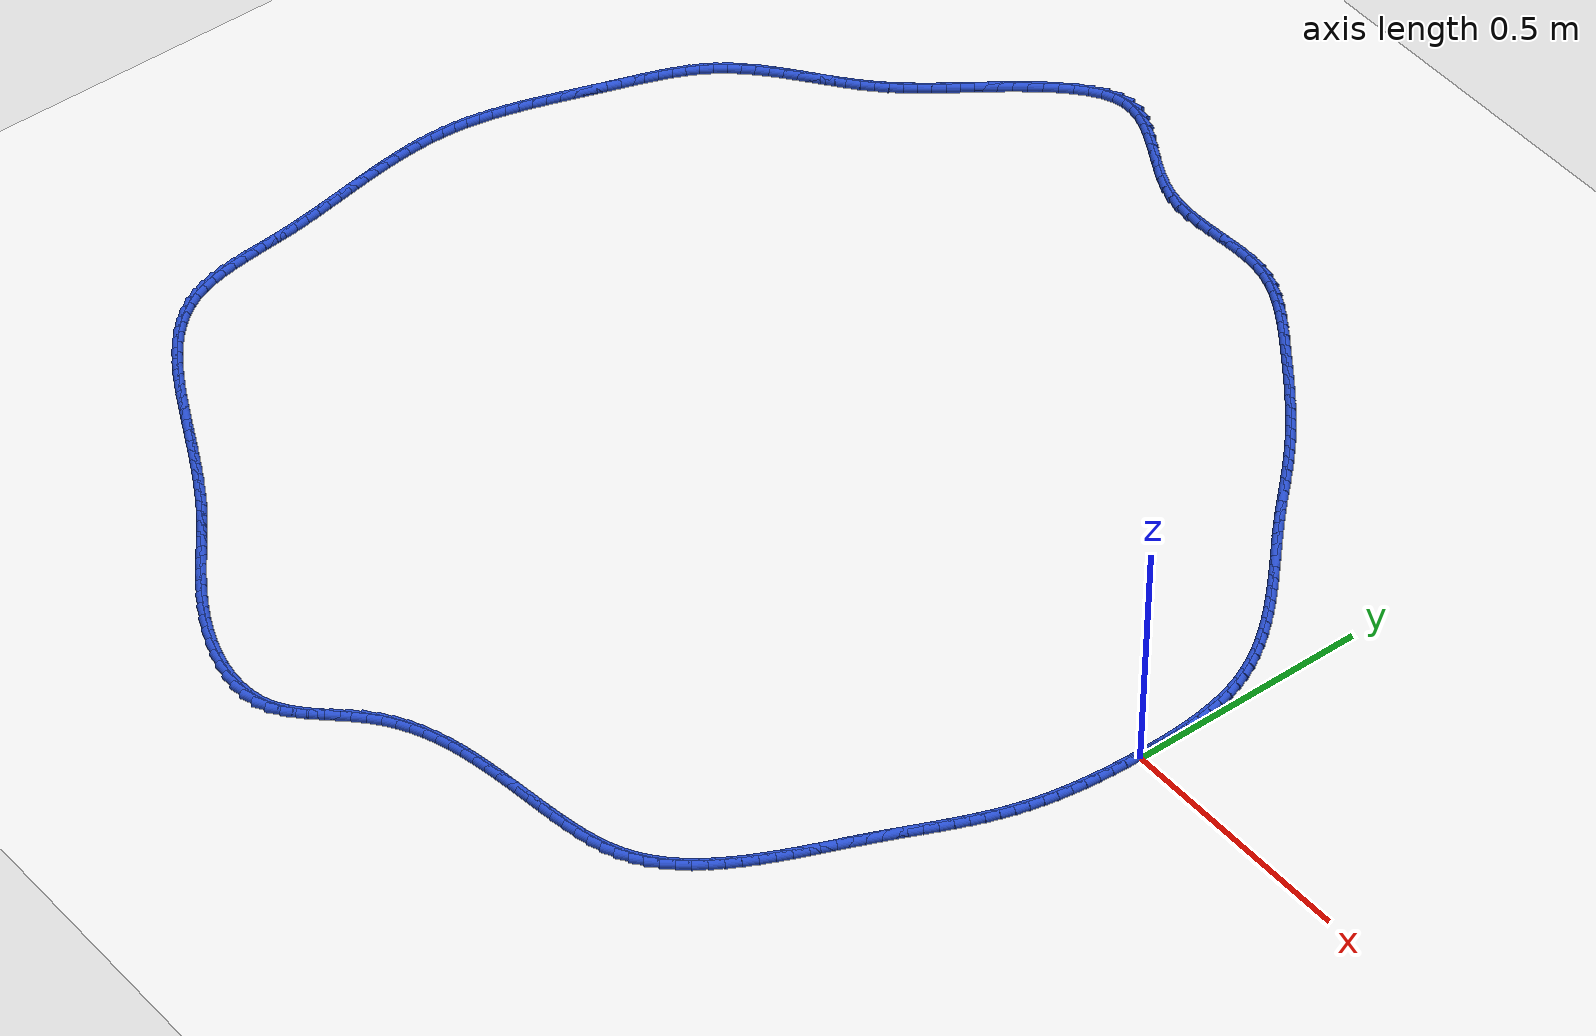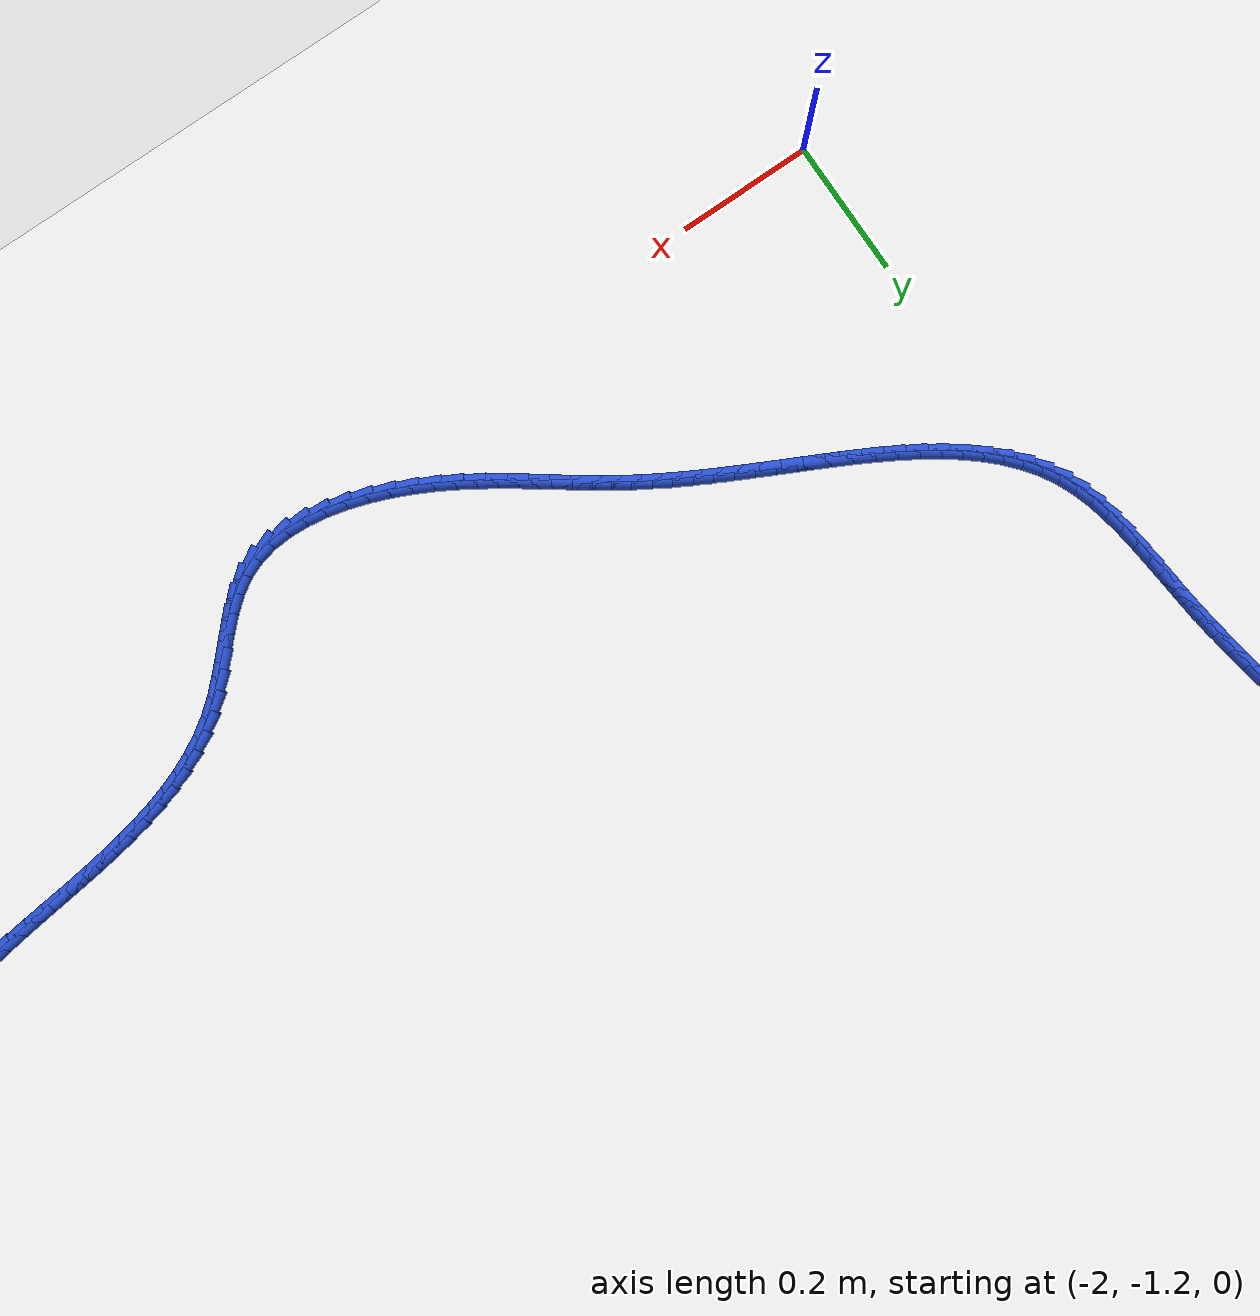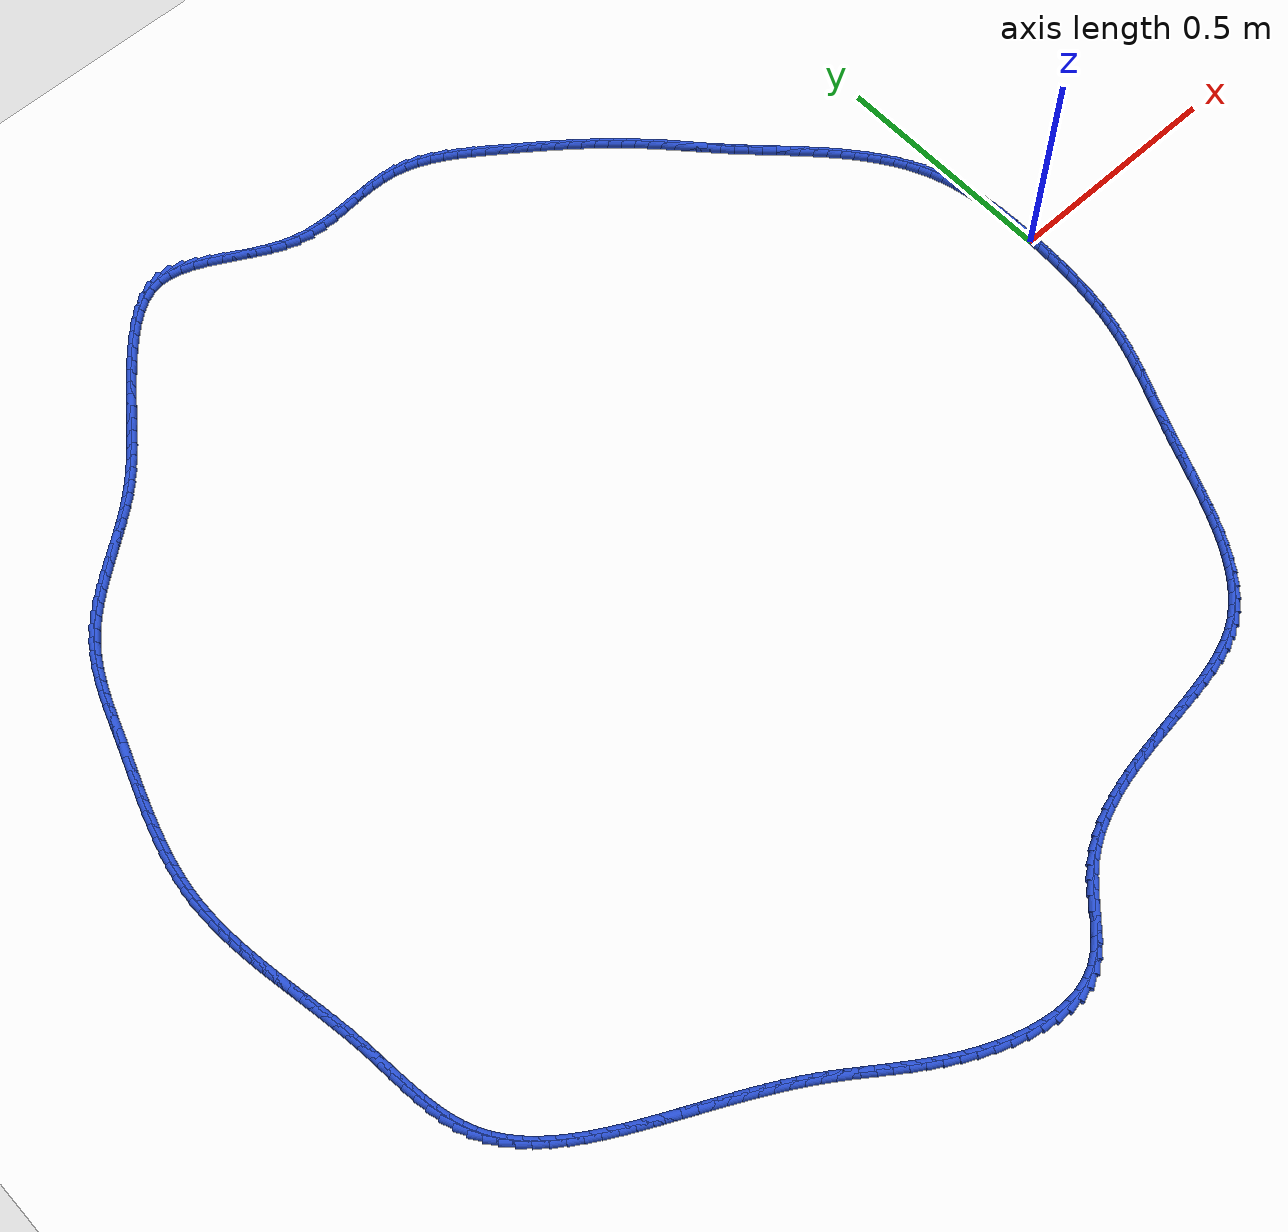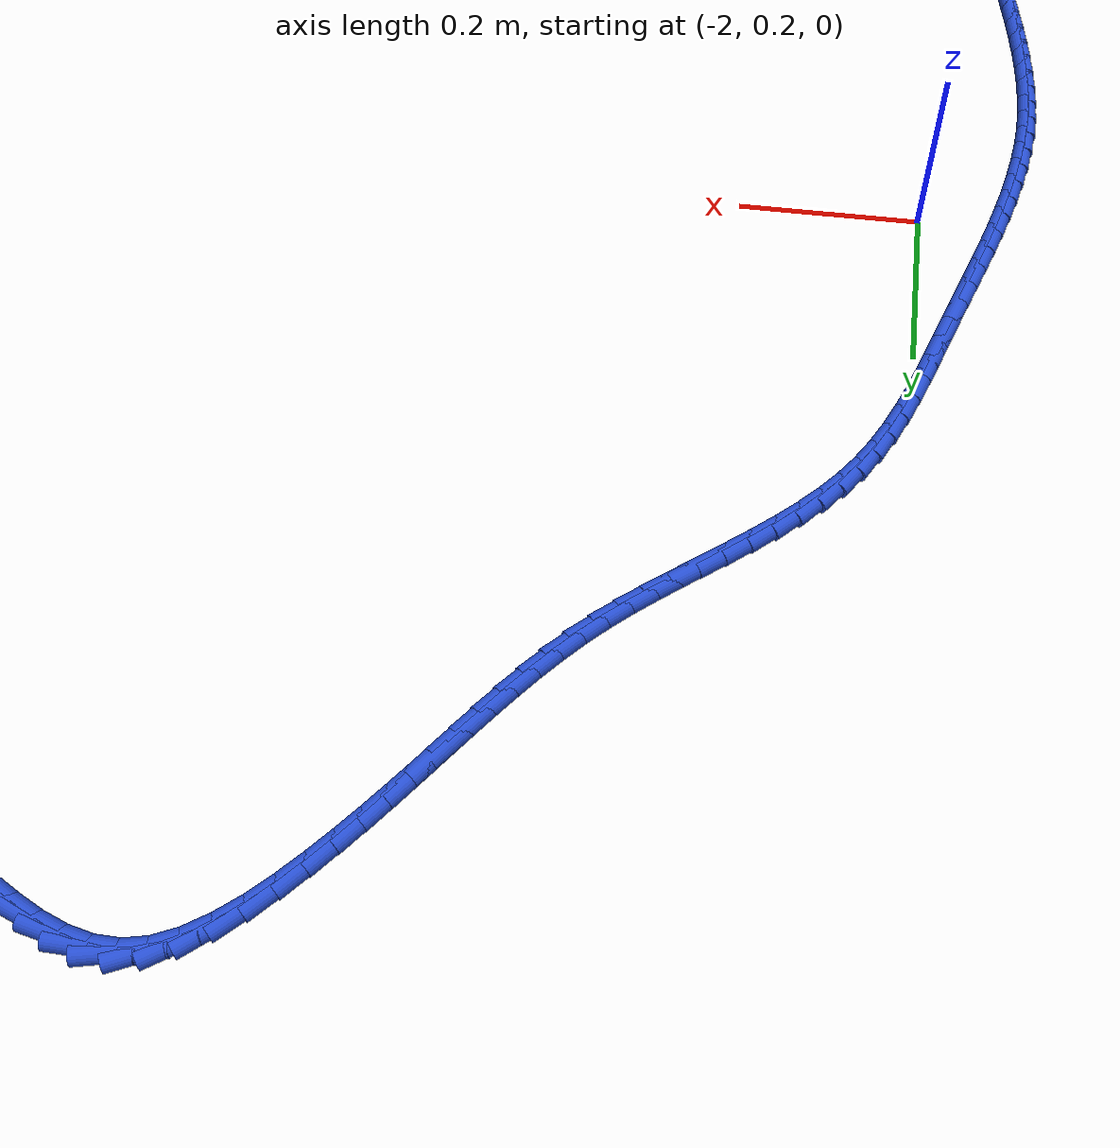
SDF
<sdf version="1.6">
 <world name="default">
  <light name="sun" type="directional">
   <pose>0 0 10 0 -0 0</pose>
   <diffuse>0.8 0.8 0.8 1</diffuse>
   <specular>0.2 0.2 0.2 1</specular>
   <attenuation>
    <range>1000</range>
    <constant>0.9</constant>
    <linear>0.01</linear>
    <quadratic>0.001</quadratic>
   </attenuation>
   <direction>-0.5 0.1 -0.9</direction>
  </light>
  <model name="ground_plane">
   <static>1</static>
   <link name="link">
    <collision name="collision">
     <geometry><plane><normal>0 0 1</normal><size>100 100</size></plane></geometry>
     <surface><friction><ode><mu>100</mu><mu2>50</mu2></ode></friction></surface>
    </collision>
    <visual name="visual">
     <cast_shadows>0</cast_shadows>
     <geometry><plane><normal>0 0 1</normal><size>100 100</size></plane></geometry>
     <material>
      <script><uri>file://media/materials/scripts/gazebo.material</uri><name>Gazebo/WhiteGlow</name></script>
     </material>
    </visual>
   </link>
  </model>
  <gravity>0 0 -9.8</gravity>
  <magnetic_field>6e-06 2.3e-05 -4.2e-05</magnetic_field>
  <atmosphere type="adiabatic"/>
  <physics name="default_physics" default="0" type="ode">
   <max_step_size>0.001</max_step_size>
   <real_time_factor>1</real_time_factor>
   <real_time_update_rate>1000</real_time_update_rate>
  </physics>
  <scene><ambient>0.4 0.4 0.4 1</ambient><background>0.7 0.7 0.7 1</background><shadows>1</shadows></scene>
  <spherical_coordinates>
   <surface_model>EARTH_WGS84</surface_model>
   <latitude_deg>0</latitude_deg>
   <longitude_deg>0</longitude_deg>
   <elevation>0</elevation>
   <heading_deg>0</heading_deg>
  </spherical_coordinates>
  <model name="line">
   <link name="link_0">
    <pose>-1.3010426069826053e-18 2.7755575615628914e-17 0.01 0 1.57 1.5606672508176465</pose>
    <collision name="collision">
     <geometry><cylinder><radius>0.01</radius><length>0.08</length></cylinder></geometry>
    </collision>
    <visual name="visual">
     <material>
      <script><name>Gazebo/Blue</name><uri>file://media/materials/scripts/gazebo.material</uri></script>
     </material>
     <geometry><cylinder><radius>0.01</radius><length>0.08</length></cylinder></geometry>
    </visual>
   </link>
   <link name="link_1">
    <pose>0.00029424484520720407 0.029048531455782754 0.01 0 1.57 -1.5596097103609743</pose>
    <collision name="collision">
     <geometry><cylinder><radius>0.01</radius><length>0.08</length></cylinder></geometry>
    </collision>
    <visual name="visual">
     <material>
      <script><name>Gazebo/Blue</name><uri>file://media/materials/scripts/gazebo.material</uri></script>
     </material>
     <geometry><cylinder><radius>0.01</radius><length>0.08</length></cylinder></geometry>
    </visual>
   </link>
   <link name="link_2">
    <pose>-3.072724350105713e-05 0.058097398448196794 0.01 0 1.57 -1.5331802799537766</pose>
    <collision name="collision">
     <geometry><cylinder><radius>0.01</radius><length>0.08</length></cylinder></geometry>
    </collision>
    <visual name="visual">
     <material>
      <script><name>Gazebo/Blue</name><uri>file://media/materials/scripts/gazebo.material</uri></script>
     </material>
     <geometry><cylinder><radius>0.01</radius><length>0.08</length></cylinder></geometry>
    </visual>
   </link>
   <link name="link_3">
    <pose>-0.0011201551349901487 0.0870455229754776 0.01 0 1.57 -1.501364476305946</pose>
    <collision name="collision">
     <geometry><cylinder><radius>0.01</radius><length>0.08</length></cylinder></geometry>
    </collision>
    <visual name="visual">
     <material>
      <script><name>Gazebo/Blue</name><uri>file://media/materials/scripts/gazebo.material</uri></script>
     </material>
     <geometry><cylinder><radius>0.01</radius><length>0.08</length></cylinder></geometry>
    </visual>
   </link>
   <link name="link_4">
    <pose>-0.0031192776981254365 0.11579182703586059 0.01 0 1.57 -1.463833048337355</pose>
    <collision name="collision">
     <geometry><cylinder><radius>0.01</radius><length>0.08</length></cylinder></geometry>
    </collision>
    <visual name="visual">
     <material>
      <script><name>Gazebo/Blue</name><uri>file://media/materials/scripts/gazebo.material</uri></script>
     </material>
     <geometry><cylinder><radius>0.01</radius><length>0.08</length></cylinder></geometry>
    </visual>
   </link>
   <link name="link_5">
    <pose>-0.006173333801772286 0.1442352326275812 0.01 0 1.57 -1.4202216440338022</pose>
    <collision name="collision">
     <geometry><cylinder><radius>0.01</radius><length>0.08</length></cylinder></geometry>
    </collision>
    <visual name="visual">
     <material>
      <script><name>Gazebo/Blue</name><uri>file://media/materials/scripts/gazebo.material</uri></script>
     </material>
     <geometry><cylinder><radius>0.01</radius><length>0.08</length></cylinder></geometry>
    </visual>
   </link>
   <link name="link_6">
    <pose>-0.010427562314796067 0.1722746617488749 0.01 0 1.57 -1.3701633984199193</pose>
    <collision name="collision">
     <geometry><cylinder><radius>0.01</radius><length>0.08</length></cylinder></geometry>
    </collision>
    <visual name="visual">
     <material>
      <script><name>Gazebo/Blue</name><uri>file://media/materials/scripts/gazebo.material</uri></script>
     </material>
     <geometry><cylinder><radius>0.01</radius><length>0.08</length></cylinder></geometry>
    </visual>
   </link>
   <link name="link_7">
    <pose>-0.01602720210606214 0.1998090363979772 0.01 0 1.57 -1.313336805617156</pose>
    <collision name="collision">
     <geometry><cylinder><radius>0.01</radius><length>0.08</length></cylinder></geometry>
    </collision>
    <visual name="visual">
     <material>
      <script><name>Gazebo/Blue</name><uri>file://media/materials/scripts/gazebo.material</uri></script>
     </material>
     <geometry><cylinder><radius>0.01</radius><length>0.08</length></cylinder></geometry>
    </visual>
   </link>
   <link name="link_8">
    <pose>-0.023117492044435868 0.22673727857312329 0.01 0 1.57 -1.2495320429789014</pose>
    <collision name="collision">
     <geometry><cylinder><radius>0.01</radius><length>0.08</length></cylinder></geometry>
    </collision>
    <visual name="visual">
     <material>
      <script><name>Gazebo/Blue</name><uri>file://media/materials/scripts/gazebo.material</uri></script>
     </material>
     <geometry><cylinder><radius>0.01</radius><length>0.08</length></cylinder></geometry>
    </visual>
   </link>
   <link name="link_9">
    <pose>-0.03184367099878263 0.2529583102725489 0.01 0 1.57 -1.1796870316313597</pose>
    <collision name="collision">
     <geometry><cylinder><radius>0.01</radius><length>0.08</length></cylinder></geometry>
    </collision>
    <visual name="visual">
     <material>
      <script><name>Gazebo/Blue</name><uri>file://media/materials/scripts/gazebo.material</uri></script>
     </material>
     <geometry><cylinder><radius>0.01</radius><length>0.08</length></cylinder></geometry>
    </visual>
   </link>
   <link name="link_10">
    <pose>-0.04232801890804924 0.2783840191710974 0.01 0 1.57 -1.111845633094564</pose>
    <collision name="collision">
     <geometry><cylinder><radius>0.01</radius><length>0.08</length></cylinder></geometry>
    </collision>
    <visual name="visual">
     <material>
      <script><name>Gazebo/Blue</name><uri>file://media/materials/scripts/gazebo.material</uri></script>
     </material>
     <geometry><cylinder><radius>0.01</radius><length>0.08</length></cylinder></geometry>
    </visual>
   </link>
   <link name="link_11">
    <pose>-0.054507199077999474 0.3030311168725808 0.01 0 1.57 -1.05029309112493</pose>
    <collision name="collision">
     <geometry><cylinder><radius>0.01</radius><length>0.08</length></cylinder></geometry>
    </collision>
    <visual name="visual">
     <material>
      <script><name>Gazebo/Blue</name><uri>file://media/materials/scripts/gazebo.material</uri></script>
     </material>
     <geometry><cylinder><radius>0.01</radius><length>0.08</length></cylinder></geometry>
    </visual>
   </link>
   <link name="link_12">
    <pose>-0.06822800848616067 0.326967065505945 0.01 0 1.57 -0.9953735546984731</pose>
    <collision name="collision">
     <geometry><cylinder><radius>0.01</radius><length>0.08</length></cylinder></geometry>
    </collision>
    <visual name="visual">
     <material>
      <script><name>Gazebo/Blue</name><uri>file://media/materials/scripts/gazebo.material</uri></script>
     </material>
     <geometry><cylinder><radius>0.01</radius><length>0.08</length></cylinder></geometry>
    </visual>
   </link>
   <link name="link_13">
    <pose>-0.08333665587410875 0.3502596593966771 0.01 0 1.57 -0.9471667919775371</pose>
    <collision name="collision">
     <geometry><cylinder><radius>0.01</radius><length>0.08</length></cylinder></geometry>
    </collision>
    <visual name="visual">
     <material>
      <script><name>Gazebo/Blue</name><uri>file://media/materials/scripts/gazebo.material</uri></script>
     </material>
     <geometry><cylinder><radius>0.01</radius><length>0.08</length></cylinder></geometry>
    </visual>
   </link>
   <link name="link_14">
    <pose>-0.09967934998341976 0.37297669287026447 0.01 0 1.57 -0.9055844722390366</pose>
    <collision name="collision">
     <geometry><cylinder><radius>0.01</radius><length>0.08</length></cylinder></geometry>
    </collision>
    <visual name="visual">
     <material>
      <script><name>Gazebo/Blue</name><uri>file://media/materials/scripts/gazebo.material</uri></script>
     </material>
     <geometry><cylinder><radius>0.01</radius><length>0.08</length></cylinder></geometry>
    </visual>
   </link>
   <link name="link_15">
    <pose>-0.11710229955566973 0.3951859602521946 0.01 0 1.57 -0.8704366464081991</pose>
    <collision name="collision">
     <geometry><cylinder><radius>0.01</radius><length>0.08</length></cylinder></geometry>
    </collision>
    <visual name="visual">
     <material>
      <script><name>Gazebo/Blue</name><uri>file://media/materials/scripts/gazebo.material</uri></script>
     </material>
     <geometry><cylinder><radius>0.01</radius><length>0.08</length></cylinder></geometry>
    </visual>
   </link>
   <link name="link_16">
    <pose>-0.13545171333243466 0.41695525586795473 0.01 0 1.57 -0.8414862653843532</pose>
    <collision name="collision">
     <geometry><cylinder><radius>0.01</radius><length>0.08</length></cylinder></geometry>
    </collision>
    <visual name="visual">
     <material>
      <script><name>Gazebo/Blue</name><uri>file://media/materials/scripts/gazebo.material</uri></script>
     </material>
     <geometry><cylinder><radius>0.01</radius><length>0.08</length></cylinder></geometry>
    </visual>
   </link>
   <link name="link_17">
    <pose>-0.15457380005529056 0.4383523740430322 0.01 0 1.57 -0.8184902678183444</pose>
    <collision name="collision">
     <geometry><cylinder><radius>0.01</radius><length>0.08</length></cylinder></geometry>
    </collision>
    <visual name="visual">
     <material>
      <script><name>Gazebo/Blue</name><uri>file://media/materials/scripts/gazebo.material</uri></script>
     </material>
     <geometry><cylinder><radius>0.01</radius><length>0.08</length></cylinder></geometry>
    </visual>
   </link>
   <link name="link_18">
    <pose>-0.17431476846581348 0.4594451091029142 0.01 0 1.57 -0.801228611935672</pose>
    <collision name="collision">
     <geometry><cylinder><radius>0.01</radius><length>0.08</length></cylinder></geometry>
    </collision>
    <visual name="visual">
     <material>
      <script><name>Gazebo/Blue</name><uri>file://media/materials/scripts/gazebo.material</uri></script>
     </material>
     <geometry><cylinder><radius>0.01</radius><length>0.08</length></cylinder></geometry>
    </visual>
   </link>
   <link name="link_19">
    <pose>-0.19452082730557935 0.4803012553730882 0.01 0 1.57 -0.7895237313646777</pose>
    <collision name="collision">
     <geometry><cylinder><radius>0.01</radius><length>0.08</length></cylinder></geometry>
    </collision>
    <visual name="visual">
     <material>
      <script><name>Gazebo/Blue</name><uri>file://media/materials/scripts/gazebo.material</uri></script>
     </material>
     <geometry><cylinder><radius>0.01</radius><length>0.08</length></cylinder></geometry>
    </visual>
   </link>
   <link name="link_20">
    <pose>-0.21503818531616423 0.5009886071790414 0.01 0 1.57 -0.7832529499221703</pose>
    <collision name="collision">
     <geometry><cylinder><radius>0.01</radius><length>0.08</length></cylinder></geometry>
    </collision>
    <visual name="visual">
     <material>
      <script><name>Gazebo/Blue</name><uri>file://media/materials/scripts/gazebo.material</uri></script>
     </material>
     <geometry><cylinder><radius>0.01</radius><length>0.08</length></cylinder></geometry>
    </visual>
   </link>
   <link name="link_21">
    <pose>-0.23571305123914416 0.5215749588462613 0.01 0 1.57 -0.7823559349784218</pose>
    <collision name="collision">
     <geometry><cylinder><radius>0.01</radius><length>0.08</length></cylinder></geometry>
    </collision>
    <visual name="visual">
     <material>
      <script><name>Gazebo/Blue</name><uri>file://media/materials/scripts/gazebo.material</uri></script>
     </material>
     <geometry><cylinder><radius>0.01</radius><length>0.08</length></cylinder></geometry>
    </visual>
   </link>
   <link name="link_22">
    <pose>-0.2563916338160951 0.5421281047002351 0.01 0 1.57 -0.7868386246211607</pose>
    <collision name="collision">
     <geometry><cylinder><radius>0.01</radius><length>0.08</length></cylinder></geometry>
    </collision>
    <visual name="visual">
     <material>
      <script><name>Gazebo/Blue</name><uri>file://media/materials/scripts/gazebo.material</uri></script>
     </material>
     <geometry><cylinder><radius>0.01</radius><length>0.08</length></cylinder></geometry>
    </visual>
   </link>
   <link name="link_23">
    <pose>-0.2769201417885931 0.5627158390664503 0.01 0 1.57 -0.7967743763249812</pose>
    <collision name="collision">
     <geometry><cylinder><radius>0.01</radius><length>0.08</length></cylinder></geometry>
    </collision>
    <visual name="visual">
     <material>
      <script><name>Gazebo/Blue</name><uri>file://media/materials/scripts/gazebo.material</uri></script>
     </material>
     <geometry><cylinder><radius>0.01</radius><length>0.08</length></cylinder></geometry>
    </visual>
   </link>
   <link name="link_24">
    <pose>-0.29714478389821414 0.5834059562703939 0.01 0 1.57 -0.8114350848497028</pose>
    <collision name="collision">
     <geometry><cylinder><radius>0.01</radius><length>0.08</length></cylinder></geometry>
    </collision>
    <visual name="visual">
     <material>
      <script><name>Gazebo/Blue</name><uri>file://media/materials/scripts/gazebo.material</uri></script>
     </material>
     <geometry><cylinder><radius>0.01</radius><length>0.08</length></cylinder></geometry>
    </visual>
   </link>
   <link name="link_25">
    <pose>-0.31693377315655075 0.6042532278141843 0.01 0 1.57 -0.8235750411063438</pose>
    <collision name="collision">
     <geometry><cylinder><radius>0.01</radius><length>0.08</length></cylinder></geometry>
    </collision>
    <visual name="visual">
     <material>
      <script><name>Gazebo/Blue</name><uri>file://media/materials/scripts/gazebo.material</uri></script>
     </material>
     <geometry><cylinder><radius>0.01</radius><length>0.08</length></cylinder></geometry>
    </visual>
   </link>
   <link name="link_26">
    <pose>-0.33634140147859237 0.6252022978160319 0.01 0 1.57 -0.8293948171005181</pose>
    <collision name="collision">
     <geometry><cylinder><radius>0.01</radius><length>0.08</length></cylinder></geometry>
    </collision>
    <visual name="visual">
     <material>
      <script><name>Gazebo/Blue</name><uri>file://media/materials/scripts/gazebo.material</uri></script>
     </material>
     <geometry><cylinder><radius>0.01</radius><length>0.08</length></cylinder></geometry>
    </visual>
   </link>
   <link name="link_27">
    <pose>-0.3555155137251957 0.6461424428000953 0.01 0 1.57 -0.8287426240895144</pose>
    <collision name="collision">
     <geometry><cylinder><radius>0.01</radius><length>0.08</length></cylinder></geometry>
    </collision>
    <visual name="visual">
     <material>
      <script><name>Gazebo/Blue</name><uri>file://media/materials/scripts/gazebo.material</uri></script>
     </material>
     <geometry><cylinder><radius>0.01</radius><length>0.08</length></cylinder></geometry>
    </visual>
   </link>
   <link name="link_28">
    <pose>-0.37460466301634393 0.666962520120366 0.01 0 1.57 -0.8215190716005674</pose>
    <collision name="collision">
     <geometry><cylinder><radius>0.01</radius><length>0.08</length></cylinder></geometry>
    </collision>
    <visual name="visual">
     <material>
      <script><name>Gazebo/Blue</name><uri>file://media/materials/scripts/gazebo.material</uri></script>
     </material>
     <geometry><cylinder><radius>0.01</radius><length>0.08</length></cylinder></geometry>
    </visual>
   </link>
   <link name="link_29">
    <pose>-0.3937574024720208 0.6875513871308371 0.01 0 1.57 -0.8076515008157712</pose>
    <collision name="collision">
     <geometry><cylinder><radius>0.01</radius><length>0.08</length></cylinder></geometry>
    </collision>
    <visual name="visual">
     <material>
      <script><name>Gazebo/Blue</name><uri>file://media/materials/scripts/gazebo.material</uri></script>
     </material>
     <geometry><cylinder><radius>0.01</radius><length>0.08</length></cylinder></geometry>
    </visual>
   </link>
   <link name="link_30">
    <pose>-0.41312228521220945 0.7077979011855001 0.01 0 1.57 -0.7872033452568612</pose>
    <collision name="collision">
     <geometry><cylinder><radius>0.01</radius><length>0.08</length></cylinder></geometry>
    </collision>
    <visual name="visual">
     <material>
      <script><name>Gazebo/Blue</name><uri>file://media/materials/scripts/gazebo.material</uri></script>
     </material>
     <geometry><cylinder><radius>0.01</radius><length>0.08</length></cylinder></geometry>
    </visual>
   </link>
   <link name="link_31">
    <pose>-0.43284591424252017 0.7275928685466158 0.01 0 1.57 -0.7637632232924442</pose>
    <collision name="collision">
     <geometry><cylinder><radius>0.01</radius><length>0.08</length></cylinder></geometry>
    </collision>
    <visual name="visual">
     <material>
      <script><name>Gazebo/Blue</name><uri>file://media/materials/scripts/gazebo.material</uri></script>
     </material>
     <geometry><cylinder><radius>0.01</radius><length>0.08</length></cylinder></geometry>
    </visual>
   </link>
   <link name="link_32">
    <pose>-0.4530044532752253 0.7468974912045723 0.01 0 1.57 -0.7418925420000578</pose>
    <collision name="collision">
     <geometry><cylinder><radius>0.01</radius><length>0.08</length></cylinder></geometry>
    </collision>
    <visual name="visual">
     <material>
      <script><name>Gazebo/Blue</name><uri>file://media/materials/scripts/gazebo.material</uri></script>
     </material>
     <geometry><cylinder><radius>0.01</radius><length>0.08</length></cylinder></geometry>
    </visual>
   </link>
   <link name="link_33">
    <pose>-0.4735855544528302 0.7657614279769895 0.01 0 1.57 -0.7219534350606516</pose>
    <collision name="collision">
     <geometry><cylinder><radius>0.01</radius><length>0.08</length></cylinder></geometry>
    </collision>
    <visual name="visual">
     <material>
      <script><name>Gazebo/Blue</name><uri>file://media/materials/scripts/gazebo.material</uri></script>
     </material>
     <geometry><cylinder><radius>0.01</radius><length>0.08</length></cylinder></geometry>
    </visual>
   </link>
   <link name="link_34">
    <pose>-0.49457124614737213 0.7842399579737747 0.01 0 1.57 -0.704003237530214</pose>
    <collision name="collision">
     <geometry><cylinder><radius>0.01</radius><length>0.08</length></cylinder></geometry>
    </collision>
    <visual name="visual">
     <material>
      <script><name>Gazebo/Blue</name><uri>file://media/materials/scripts/gazebo.material</uri></script>
     </material>
     <geometry><cylinder><radius>0.01</radius><length>0.08</length></cylinder></geometry>
    </visual>
   </link>
   <link name="link_35">
    <pose>-0.5159435567308883 0.8023883603048337 0.01 0 1.57 -0.6880806103003675</pose>
    <collision name="collision">
     <geometry><cylinder><radius>0.01</radius><length>0.08</length></cylinder></geometry>
    </collision>
    <visual name="visual">
     <material>
      <script><name>Gazebo/Blue</name><uri>file://media/materials/scripts/gazebo.material</uri></script>
     </material>
     <geometry><cylinder><radius>0.01</radius><length>0.08</length></cylinder></geometry>
    </visual>
   </link>
   <link name="link_36">
    <pose>-0.5376845145754158 0.820261914080074 0.01 0 1.57 -0.6742073913071734</pose>
    <collision name="collision">
     <geometry><cylinder><radius>0.01</radius><length>0.08</length></cylinder></geometry>
    </collision>
    <visual name="visual">
     <material>
      <script><name>Gazebo/Blue</name><uri>file://media/materials/scripts/gazebo.material</uri></script>
     </material>
     <geometry><cylinder><radius>0.01</radius><length>0.08</length></cylinder></geometry>
    </visual>
   </link>
   <link name="link_37">
    <pose>-0.5597761480529915 0.8379158984094014 0.01 0 1.57 -0.6623905473552284</pose>
    <collision name="collision">
     <geometry><cylinder><radius>0.01</radius><length>0.08</length></cylinder></geometry>
    </collision>
    <visual name="visual">
     <material>
      <script><name>Gazebo/Blue</name><uri>file://media/materials/scripts/gazebo.material</uri></script>
     </material>
     <geometry><cylinder><radius>0.01</radius><length>0.08</length></cylinder></geometry>
    </visual>
   </link>
   <link name="link_38">
    <pose>-0.5822004855356525 0.8554055924027227 0.01 0 1.57 -0.6526241033862366</pose>
    <collision name="collision">
     <geometry><cylinder><radius>0.01</radius><length>0.08</length></cylinder></geometry>
    </collision>
    <visual name="visual">
     <material>
      <script><name>Gazebo/Blue</name><uri>file://media/materials/scripts/gazebo.material</uri></script>
     </material>
     <geometry><cylinder><radius>0.01</radius><length>0.08</length></cylinder></geometry>
    </visual>
   </link>
   <link name="link_39">
    <pose>-0.6049395553954362 0.8727862751699447 0.01 0 1.57 -0.6448909564656563</pose>
    <collision name="collision">
     <geometry><cylinder><radius>0.01</radius><length>0.08</length></cylinder></geometry>
    </collision>
    <visual name="visual">
     <material>
      <script><name>Gazebo/Blue</name><uri>file://media/materials/scripts/gazebo.material</uri></script>
     </material>
     <geometry><cylinder><radius>0.01</radius><length>0.08</length></cylinder></geometry>
    </visual>
   </link>
   <link name="link_40">
    <pose>-0.6279753860043795 0.8901132258209735 0.01 0 1.57 -0.6391645111710319</pose>
    <collision name="collision">
     <geometry><cylinder><radius>0.01</radius><length>0.08</length></cylinder></geometry>
    </collision>
    <visual name="visual">
     <material>
      <script><name>Gazebo/Blue</name><uri>file://media/materials/scripts/gazebo.material</uri></script>
     </material>
     <geometry><cylinder><radius>0.01</radius><length>0.08</length></cylinder></geometry>
    </visual>
   </link>
   <link name="link_41">
    <pose>-0.6512900057345197 0.9074417234657162 0.01 0 1.57 -0.6339264964163984</pose>
    <collision name="collision">
     <geometry><cylinder><radius>0.01</radius><length>0.08</length></cylinder></geometry>
    </collision>
    <visual name="visual">
     <material>
      <script><name>Gazebo/Blue</name><uri>file://media/materials/scripts/gazebo.material</uri></script>
     </material>
     <geometry><cylinder><radius>0.01</radius><length>0.08</length></cylinder></geometry>
    </visual>
   </link>
   <link name="link_42">
    <pose>-0.6748719996079549 0.9247779291292683 0.01 0 1.57 -0.6193008657885577</pose>
    <collision name="collision">
     <geometry><cylinder><radius>0.01</radius><length>0.08</length></cylinder></geometry>
    </collision>
    <visual name="visual">
     <material>
      <script><name>Gazebo/Blue</name><uri>file://media/materials/scripts/gazebo.material</uri></script>
     </material>
     <geometry><cylinder><radius>0.01</radius><length>0.08</length></cylinder></geometry>
    </visual>
   </link>
   <link name="link_43">
    <pose>-0.6987534782917921 0.9418019384980377 0.01 0 1.57 -0.5910021646953973</pose>
    <collision name="collision">
     <geometry><cylinder><radius>0.01</radius><length>0.08</length></cylinder></geometry>
    </collision>
    <visual name="visual">
     <material>
      <script><name>Gazebo/Blue</name><uri>file://media/materials/scripts/gazebo.material</uri></script>
     </material>
     <geometry><cylinder><radius>0.01</radius><length>0.08</length></cylinder></geometry>
    </visual>
   </link>
   <link name="link_44">
    <pose>-0.72298428520006 0.9580610052493113 0.01 0 1.57 -0.5482331402213708</pose>
    <collision name="collision">
     <geometry><cylinder><radius>0.01</radius><length>0.08</length></cylinder></geometry>
    </collision>
    <visual name="visual">
     <material>
      <script><name>Gazebo/Blue</name><uri>file://media/materials/scripts/gazebo.material</uri></script>
     </material>
     <geometry><cylinder><radius>0.01</radius><length>0.08</length></cylinder></geometry>
    </visual>
   </link>
   <link name="link_45">
    <pose>-0.7476143156811834 0.9731019940022443 0.01 0 1.57 -0.4897781574068066</pose>
    <collision name="collision">
     <geometry><cylinder><radius>0.01</radius><length>0.08</length></cylinder></geometry>
    </collision>
    <visual name="visual">
     <material>
      <script><name>Gazebo/Blue</name><uri>file://media/materials/scripts/gazebo.material</uri></script>
     </material>
     <geometry><cylinder><radius>0.01</radius><length>0.08</length></cylinder></geometry>
    </visual>
   </link>
   <link name="link_46">
    <pose>-0.7726934650835866 0.9864717693759908 0.01 0 1.57 -0.4142131788075716</pose>
    <collision name="collision">
     <geometry><cylinder><radius>0.01</radius><length>0.08</length></cylinder></geometry>
    </collision>
    <visual name="visual">
     <material>
      <script><name>Gazebo/Blue</name><uri>file://media/materials/scripts/gazebo.material</uri></script>
     </material>
     <geometry><cylinder><radius>0.01</radius><length>0.08</length></cylinder></geometry>
    </visual>
   </link>
   <link name="link_47">
    <pose>-0.7982716287556936 0.9977171959897045 0.01 0 1.57 -0.32033473618473374</pose>
    <collision name="collision">
     <geometry><cylinder><radius>0.01</radius><length>0.08</length></cylinder></geometry>
    </collision>
    <visual name="visual">
     <material>
      <script><name>Gazebo/Blue</name><uri>file://media/materials/scripts/gazebo.material</uri></script>
     </material>
     <geometry><cylinder><radius>0.01</radius><length>0.08</length></cylinder></geometry>
    </visual>
   </link>
   <link name="link_48">
    <pose>-0.824398702045929 1.0063851384625404 0.01 0 1.57 -0.20826086767417049</pose>
    <collision name="collision">
     <geometry><cylinder><radius>0.01</radius><length>0.08</length></cylinder></geometry>
    </collision>
    <visual name="visual">
     <material>
      <script><name>Gazebo/Blue</name><uri>file://media/materials/scripts/gazebo.material</uri></script>
     </material>
     <geometry><cylinder><radius>0.01</radius><length>0.08</length></cylinder></geometry>
    </visual>
   </link>
   <link name="link_49">
    <pose>-0.8511232969175112 1.0120327128234734 0.01 0 1.57 -0.0971254992680046</pose>
    <collision name="collision">
     <geometry><cylinder><radius>0.01</radius><length>0.08</length></cylinder></geometry>
    </collision>
    <visual name="visual">
     <material>
      <script><name>Gazebo/Blue</name><uri>file://media/materials/scripts/gazebo.material</uri></script>
     </material>
     <geometry><cylinder><radius>0.01</radius><length>0.08</length></cylinder></geometry>
    </visual>
   </link>
   <link name="link_50">
    <pose>-0.8784343529677014 1.0146936853509863 0.01 0 1.57 -0.0135497071879427</pose>
    <collision name="collision">
     <geometry><cylinder><radius>0.01</radius><length>0.08</length></cylinder></geometry>
    </collision>
    <visual name="visual">
     <material>
      <script><name>Gazebo/Blue</name><uri>file://media/materials/scripts/gazebo.material</uri></script>
     </material>
     <geometry><cylinder><radius>0.01</radius><length>0.08</length></cylinder></geometry>
    </visual>
   </link>
   <link name="link_51">
    <pose>-0.9062371063712255 1.0150704275748463 0.01 0 1.57 0.040947311922326195</pose>
    <collision name="collision">
     <geometry><cylinder><radius>0.01</radius><length>0.08</length></cylinder></geometry>
    </collision>
    <visual name="visual">
     <material>
      <script><name>Gazebo/Blue</name><uri>file://media/materials/scripts/gazebo.material</uri></script>
     </material>
     <geometry><cylinder><radius>0.01</radius><length>0.08</length></cylinder></geometry>
    </visual>
   </link>
   <link name="link_52">
    <pose>-0.9344305304965821 1.0139153369975247 0.01 0 1.57 0.06781430517034934</pose>
    <collision name="collision">
     <geometry><cylinder><radius>0.01</radius><length>0.08</length></cylinder></geometry>
    </collision>
    <visual name="visual">
     <material>
      <script><name>Gazebo/Blue</name><uri>file://media/materials/scripts/gazebo.material</uri></script>
     </material>
     <geometry><cylinder><radius>0.01</radius><length>0.08</length></cylinder></geometry>
    </visual>
   </link>
   <link name="link_53">
    <pose>-0.9629135987122699 1.0119808111214916 0.01 0 1.57 0.06830822056251305</pose>
    <collision name="collision">
     <geometry><cylinder><radius>0.01</radius><length>0.08</length></cylinder></geometry>
    </collision>
    <visual name="visual">
     <material>
      <script><name>Gazebo/Blue</name><uri>file://media/materials/scripts/gazebo.material</uri></script>
     </material>
     <geometry><cylinder><radius>0.01</radius><length>0.08</length></cylinder></geometry>
    </visual>
   </link>
   <link name="link_54">
    <pose>-0.9915852843867886 1.010019247449219 0.01 0 1.57 0.04295808496216087</pose>
    <collision name="collision">
     <geometry><cylinder><radius>0.01</radius><length>0.08</length></cylinder></geometry>
    </collision>
    <visual name="visual">
     <material>
      <script><name>Gazebo/Blue</name><uri>file://media/materials/scripts/gazebo.material</uri></script>
     </material>
     <geometry><cylinder><radius>0.01</radius><length>0.08</length></cylinder></geometry>
    </visual>
   </link>
   <link name="link_55">
    <pose>-1.0203445608886357 1.0087830434831766 0.01 0 1.57 -0.008402869825890825</pose>
    <collision name="collision">
     <geometry><cylinder><radius>0.01</radius><length>0.08</length></cylinder></geometry>
    </collision>
    <visual name="visual">
     <material>
      <script><name>Gazebo/Blue</name><uri>file://media/materials/scripts/gazebo.material</uri></script>
     </material>
     <geometry><cylinder><radius>0.01</radius><length>0.08</length></cylinder></geometry>
    </visual>
   </link>
   <link name="link_56">
    <pose>-1.0490904015863114 1.0090245967258367 0.01 0 1.57 -0.08611513555287685</pose>
    <collision name="collision">
     <geometry><cylinder><radius>0.01</radius><length>0.08</length></cylinder></geometry>
    </collision>
    <visual name="visual">
     <material>
      <script><name>Gazebo/Blue</name><uri>file://media/materials/scripts/gazebo.material</uri></script>
     </material>
     <geometry><cylinder><radius>0.01</radius><length>0.08</length></cylinder></geometry>
    </visual>
   </link>
   <link name="link_57">
    <pose>-1.0777217798483143 1.0114963046796694 0.01 0 1.57 -0.18963756729086753</pose>
    <collision name="collision">
     <geometry><cylinder><radius>0.01</radius><length>0.08</length></cylinder></geometry>
    </collision>
    <visual name="visual">
     <material>
      <script><name>Gazebo/Blue</name><uri>file://media/materials/scripts/gazebo.material</uri></script>
     </material>
     <geometry><cylinder><radius>0.01</radius><length>0.08</length></cylinder></geometry>
    </visual>
   </link>
   <link name="link_58">
    <pose>-1.1061376690431433 1.0169505648471462 0.01 0 1.57 -0.31014908968528165</pose>
    <collision name="collision">
     <geometry><cylinder><radius>0.01</radius><length>0.08</length></cylinder></geometry>
    </collision>
    <visual name="visual">
     <material>
      <script><name>Gazebo/Blue</name><uri>file://media/materials/scripts/gazebo.material</uri></script>
     </material>
     <geometry><cylinder><radius>0.01</radius><length>0.08</length></cylinder></geometry>
    </visual>
   </link>
   <link name="link_59">
    <pose>-1.1342468490902466 1.025959329386577 0.01 0 1.57 -0.408121723956436</pose>
    <collision name="collision">
     <geometry><cylinder><radius>0.01</radius><length>0.08</length></cylinder></geometry>
    </collision>
    <visual name="visual">
     <material>
      <script><name>Gazebo/Blue</name><uri>file://media/materials/scripts/gazebo.material</uri></script>
     </material>
     <geometry><cylinder><radius>0.01</radius><length>0.08</length></cylinder></geometry>
    </visual>
   </link>
   <link name="link_60">
    <pose>-1.1620193161146386 1.03796814226873 0.01 0 1.57 -0.4725298005467078</pose>
    <collision name="collision">
     <geometry><cylinder><radius>0.01</radius><length>0.08</length></cylinder></geometry>
    </collision>
    <visual name="visual">
     <material>
      <script><name>Gazebo/Blue</name><uri>file://media/materials/scripts/gazebo.material</uri></script>
     </material>
     <geometry><cylinder><radius>0.01</radius><length>0.08</length></cylinder></geometry>
    </visual>
   </link>
   <link name="link_61">
    <pose>-1.1894486435583793 1.0519887132742813 0.01 0 1.57 -0.5070642484486582</pose>
    <collision name="collision">
     <geometry><cylinder><radius>0.01</radius><length>0.08</length></cylinder></geometry>
    </collision>
    <visual name="visual">
     <material>
      <script><name>Gazebo/Blue</name><uri>file://media/materials/scripts/gazebo.material</uri></script>
     </material>
     <geometry><cylinder><radius>0.01</radius><length>0.08</length></cylinder></geometry>
    </visual>
   </link>
   <link name="link_62">
    <pose>-1.2165284545049395 1.067031838757636 0.01 0 1.57 -0.5136470484361008</pose>
    <collision name="collision">
     <geometry><cylinder><radius>0.01</radius><length>0.08</length></cylinder></geometry>
    </collision>
    <visual name="visual">
     <material>
      <script><name>Gazebo/Blue</name><uri>file://media/materials/scripts/gazebo.material</uri></script>
     </material>
     <geometry><cylinder><radius>0.01</radius><length>0.08</length></cylinder></geometry>
    </visual>
   </link>
   <link name="link_63">
    <pose>-1.243252372037789 1.0821083150731985 0.01 0 1.57 -0.49175943579107173</pose>
    <collision name="collision">
     <geometry><cylinder><radius>0.01</radius><length>0.08</length></cylinder></geometry>
    </collision>
    <visual name="visual">
     <material>
      <script><name>Gazebo/Blue</name><uri>file://media/materials/scripts/gazebo.material</uri></script>
     </material>
     <geometry><cylinder><radius>0.01</radius><length>0.08</length></cylinder></geometry>
    </visual>
   </link>
   <link name="link_64">
    <pose>-1.2696140192403986 1.096228938575373 0.01 0 1.57 -0.43806363856981906</pose>
    <collision name="collision">
     <geometry><cylinder><radius>0.01</radius><length>0.08</length></cylinder></geometry>
    </collision>
    <visual name="visual">
     <material>
      <script><name>Gazebo/Blue</name><uri>file://media/materials/scripts/gazebo.material</uri></script>
     </material>
     <geometry><cylinder><radius>0.01</radius><length>0.08</length></cylinder></geometry>
    </visual>
   </link>
   <link name="link_65">
    <pose>-1.2956070191962377 1.108404505618564 0.01 0 1.57 -0.34620632339271007</pose>
    <collision name="collision">
     <geometry><cylinder><radius>0.01</radius><length>0.08</length></cylinder></geometry>
    </collision>
    <visual name="visual">
     <material>
      <script><name>Gazebo/Blue</name><uri>file://media/materials/scripts/gazebo.material</uri></script>
     </material>
     <geometry><cylinder><radius>0.01</radius><length>0.08</length></cylinder></geometry>
    </visual>
   </link>
   <link name="link_66">
    <pose>-1.3212249949887778 1.1176458125571762 0.01 0 1.57 -0.20768138611917372</pose>
    <collision name="collision">
     <geometry><cylinder><radius>0.01</radius><length>0.08</length></cylinder></geometry>
    </collision>
    <visual name="visual">
     <material>
      <script><name>Gazebo/Blue</name><uri>file://media/materials/scripts/gazebo.material</uri></script>
     </material>
     <geometry><cylinder><radius>0.01</radius><length>0.08</length></cylinder></geometry>
    </visual>
   </link>
   <link name="link_67">
    <pose>-1.3464615697014881 1.1229636557456144 0.01 0 1.57 -0.016304205568538666</pose>
    <collision name="collision">
     <geometry><cylinder><radius>0.01</radius><length>0.08</length></cylinder></geometry>
    </collision>
    <visual name="visual">
     <material>
      <script><name>Gazebo/Blue</name><uri>file://media/materials/scripts/gazebo.material</uri></script>
     </material>
     <geometry><cylinder><radius>0.01</radius><length>0.08</length></cylinder></geometry>
    </visual>
   </link>
   <link name="link_68">
    <pose>-1.3713103664178399 1.1233688315382828 0.01 0 1.57 0.21829590260100543</pose>
    <collision name="collision">
     <geometry><cylinder><radius>0.01</radius><length>0.08</length></cylinder></geometry>
    </collision>
    <visual name="visual">
     <material>
      <script><name>Gazebo/Blue</name><uri>file://media/materials/scripts/gazebo.material</uri></script>
     </material>
     <geometry><cylinder><radius>0.01</radius><length>0.08</length></cylinder></geometry>
    </visual>
   </link>
   <link name="link_69">
    <pose>-1.3957604164779591 1.1179450576303693 0.01 0 1.57 0.43227511256635154</pose>
    <collision name="collision">
     <geometry><cylinder><radius>0.01</radius><length>0.08</length></cylinder></geometry>
    </collision>
    <visual name="visual">
     <material>
      <script><name>Gazebo/Blue</name><uri>file://media/materials/scripts/gazebo.material</uri></script>
     </material>
     <geometry><cylinder><radius>0.01</radius><length>0.08</length></cylinder></geometry>
    </visual>
   </link>
   <link name="link_70">
    <pose>-1.4197308832820836 1.1068856224124266 0.01 0 1.57 0.5900061105820735</pose>
    <collision name="collision">
     <geometry><cylinder><radius>0.01</radius><length>0.08</length></cylinder></geometry>
    </collision>
    <visual name="visual">
     <material>
      <script><name>Gazebo/Blue</name><uri>file://media/materials/scripts/gazebo.material</uri></script>
     </material>
     <geometry><cylinder><radius>0.01</radius><length>0.08</length></cylinder></geometry>
    </visual>
   </link>
   <link name="link_71">
    <pose>-1.4430865452606743 1.0912475003780706 0.01 0 1.57 0.7025256998970416</pose>
    <collision name="collision">
     <geometry><cylinder><radius>0.01</radius><length>0.08</length></cylinder></geometry>
    </collision>
    <visual name="visual">
     <material>
      <script><name>Gazebo/Blue</name><uri>file://media/materials/scripts/gazebo.material</uri></script>
     </material>
     <geometry><cylinder><radius>0.01</radius><length>0.08</length></cylinder></geometry>
    </visual>
   </link>
   <link name="link_72">
    <pose>-1.465690746744254 1.0721104409197761 0.01 0 1.57 0.7817044151747691</pose>
    <collision name="collision">
     <geometry><cylinder><radius>0.01</radius><length>0.08</length></cylinder></geometry>
    </collision>
    <visual name="visual">
     <material>
      <script><name>Gazebo/Blue</name><uri>file://media/materials/scripts/gazebo.material</uri></script>
     </material>
     <geometry><cylinder><radius>0.01</radius><length>0.08</length></cylinder></geometry>
    </visual>
   </link>
   <link name="link_73">
    <pose>-1.4874068320633462 1.0505541934300189 0.01 0 1.57 0.8359291964906289</pose>
    <collision name="collision">
     <geometry><cylinder><radius>0.01</radius><length>0.08</length></cylinder></geometry>
    </collision>
    <visual name="visual">
     <material>
      <script><name>Gazebo/Blue</name><uri>file://media/materials/scripts/gazebo.material</uri></script>
     </material>
     <geometry><cylinder><radius>0.01</radius><length>0.08</length></cylinder></geometry>
    </visual>
   </link>
   <link name="link_74">
    <pose>-1.5080981455484754 1.027658507301274 0.01 0 1.57 0.8713934667841656</pose>
    <collision name="collision">
     <geometry><cylinder><radius>0.01</radius><length>0.08</length></cylinder></geometry>
    </collision>
    <visual name="visual">
     <material>
      <script><name>Gazebo/Blue</name><uri>file://media/materials/scripts/gazebo.material</uri></script>
     </material>
     <geometry><cylinder><radius>0.01</radius><length>0.08</length></cylinder></geometry>
    </visual>
   </link>
   <link name="link_75">
    <pose>-1.5276616913364012 1.0044036786773858 0.01 0 1.57 0.8979734134597531</pose>
    <collision name="collision">
     <geometry><cylinder><radius>0.01</radius><length>0.08</length></cylinder></geometry>
    </collision>
    <visual name="visual">
     <material>
      <script><name>Gazebo/Blue</name><uri>file://media/materials/scripts/gazebo.material</uri></script>
     </material>
     <geometry><cylinder><radius>0.01</radius><length>0.08</length></cylinder></geometry>
    </visual>
   </link>
   <link name="link_76">
    <pose>-1.5462136987787907 0.9811222679531879 0.01 0 1.57 0.9185829386525458</pose>
    <collision name="collision">
     <geometry><cylinder><radius>0.01</radius><length>0.08</length></cylinder></geometry>
    </collision>
    <visual name="visual">
     <material>
      <script><name>Gazebo/Blue</name><uri>file://media/materials/scripts/gazebo.material</uri></script>
     </material>
     <geometry><cylinder><radius>0.01</radius><length>0.08</length></cylinder></geometry>
    </visual>
   </link>
   <link name="link_77">
    <pose>-1.56395817879367 0.9578874709305374 0.01 0 1.57 0.9327317019199689</pose>
    <collision name="collision">
     <geometry><cylinder><radius>0.01</radius><length>0.08</length></cylinder></geometry>
    </collision>
    <visual name="visual">
     <material>
      <script><name>Gazebo/Blue</name><uri>file://media/materials/scripts/gazebo.material</uri></script>
     </material>
     <geometry><cylinder><radius>0.01</radius><length>0.08</length></cylinder></geometry>
    </visual>
   </link>
   <link name="link_78">
    <pose>-1.581099375588295 0.9347717941211714 0.01 0 1.57 0.9400022929701474</pose>
    <collision name="collision">
     <geometry><cylinder><radius>0.01</radius><length>0.08</length></cylinder></geometry>
    </collision>
    <visual name="visual">
     <material>
      <script><name>Gazebo/Blue</name><uri>file://media/materials/scripts/gazebo.material</uri></script>
     </material>
     <geometry><cylinder><radius>0.01</radius><length>0.08</length></cylinder></geometry>
    </visual>
   </link>
   <link name="link_79">
    <pose>-1.5978415333699214 0.9118477440368282 0.01 0 1.57 0.9400566881935359</pose>
    <collision name="collision">
     <geometry><cylinder><radius>0.01</radius><length>0.08</length></cylinder></geometry>
    </collision>
    <visual name="visual">
     <material>
      <script><name>Gazebo/Blue</name><uri>file://media/materials/scripts/gazebo.material</uri></script>
     </material>
     <geometry><cylinder><radius>0.01</radius><length>0.08</length></cylinder></geometry>
    </visual>
   </link>
   <link name="link_80">
    <pose>-1.614388896345806 0.8891878271892448 0.01 0 1.57 0.9326388836136437</pose>
    <collision name="collision">
     <geometry><cylinder><radius>0.01</radius><length>0.08</length></cylinder></geometry>
    </collision>
    <visual name="visual">
     <material>
      <script><name>Gazebo/Blue</name><uri>file://media/materials/scripts/gazebo.material</uri></script>
     </material>
     <geometry><cylinder><radius>0.01</radius><length>0.08</length></cylinder></geometry>
    </visual>
   </link>
   <link name="link_81">
    <pose>-1.630945708723205 0.8668645500901585 0.01 0 1.57 0.9175858003845201</pose>
    <collision name="collision">
     <geometry><cylinder><radius>0.01</radius><length>0.08</length></cylinder></geometry>
    </collision>
    <visual name="visual">
     <material>
      <script><name>Gazebo/Blue</name><uri>file://media/materials/scripts/gazebo.material</uri></script>
     </material>
     <geometry><cylinder><radius>0.01</radius><length>0.08</length></cylinder></geometry>
    </visual>
   </link>
   <link name="link_82">
    <pose>-1.6477162147093745 0.8449504192513075 0.01 0 1.57 0.8948485219744452</pose>
    <collision name="collision">
     <geometry><cylinder><radius>0.01</radius><length>0.08</length></cylinder></geometry>
    </collision>
    <visual name="visual">
     <material>
      <script><name>Gazebo/Blue</name><uri>file://media/materials/scripts/gazebo.material</uri></script>
     </material>
     <geometry><cylinder><radius>0.01</radius><length>0.08</length></cylinder></geometry>
    </visual>
   </link>
   <link name="link_83">
    <pose>-1.6649046585115697 0.8235179411844286 0.01 0 1.57 0.8645238199147148</pose>
    <collision name="collision">
     <geometry><cylinder><radius>0.01</radius><length>0.08</length></cylinder></geometry>
    </collision>
    <visual name="visual">
     <material>
      <script><name>Gazebo/Blue</name><uri>file://media/materials/scripts/gazebo.material</uri></script>
     </material>
     <geometry><cylinder><radius>0.01</radius><length>0.08</length></cylinder></geometry>
    </visual>
   </link>
   <link name="link_84">
    <pose>-1.6827152843370485 0.8026396224012599 0.01 0 1.57 0.8268928376455659</pose>
    <collision name="collision">
     <geometry><cylinder><radius>0.01</radius><length>0.08</length></cylinder></geometry>
    </collision>
    <visual name="visual">
     <material>
      <script><name>Gazebo/Blue</name><uri>file://media/materials/scripts/gazebo.material</uri></script>
     </material>
     <geometry><cylinder><radius>0.01</radius><length>0.08</length></cylinder></geometry>
    </visual>
   </link>
   <link name="link_85">
    <pose>-1.7013523363930658 0.7823879694135378 0.01 0 1.57 0.7824617821054257</pose>
    <collision name="collision">
     <geometry><cylinder><radius>0.01</radius><length>0.08</length></cylinder></geometry>
    </collision>
    <visual name="visual">
     <material>
      <script><name>Gazebo/Blue</name><uri>file://media/materials/scripts/gazebo.material</uri></script>
     </material>
     <geometry><cylinder><radius>0.01</radius><length>0.08</length></cylinder></geometry>
    </visual>
   </link>
   <link name="link_86">
    <pose>-1.7210200095322352 0.7628354620097838 0.01 0 1.57 0.7360190742335548</pose>
    <collision name="collision">
     <geometry><cylinder><radius>0.01</radius><length>0.08</length></cylinder></geometry>
    </collision>
    <visual name="visual">
     <material>
      <script><name>Gazebo/Blue</name><uri>file://media/materials/scripts/gazebo.material</uri></script>
     </material>
     <geometry><cylinder><radius>0.01</radius><length>0.08</length></cylinder></geometry>
    </visual>
   </link>
   <link name="link_87">
    <pose>-1.7418168329581214 0.7439973669997312 0.01 0 1.57 0.7003424267690751</pose>
    <collision name="collision">
     <geometry><cylinder><radius>0.01</radius><length>0.08</length></cylinder></geometry>
    </collision>
    <visual name="visual">
     <material>
      <script><name>Gazebo/Blue</name><uri>file://media/materials/scripts/gazebo.material</uri></script>
     </material>
     <geometry><cylinder><radius>0.01</radius><length>0.08</length></cylinder></geometry>
    </visual>
   </link>
   <link name="link_88">
    <pose>-1.7635123217473943 0.7257108055191752 0.01 0 1.57 0.6772686198572222</pose>
    <collision name="collision">
     <geometry><cylinder><radius>0.01</radius><length>0.08</length></cylinder></geometry>
    </collision>
    <visual name="visual">
     <material>
      <script><name>Gazebo/Blue</name><uri>file://media/materials/scripts/gazebo.material</uri></script>
     </material>
     <geometry><cylinder><radius>0.01</radius><length>0.08</length></cylinder></geometry>
    </visual>
   </link>
   <link name="link_89">
    <pose>-1.785812136681418 0.7077783246065036 0.01 0 1.57 0.6662702222797875</pose>
    <collision name="collision">
     <geometry><cylinder><radius>0.01</radius><length>0.08</length></cylinder></geometry>
    </collision>
    <visual name="visual">
     <material>
      <script><name>Gazebo/Blue</name><uri>file://media/materials/scripts/gazebo.material</uri></script>
     </material>
     <geometry><cylinder><radius>0.01</radius><length>0.08</length></cylinder></geometry>
    </visual>
   </link>
   <link name="link_90">
    <pose>-1.8084219385415554 0.6900024713001058 0.01 0 1.57 0.6670488412044291</pose>
    <collision name="collision">
     <geometry><cylinder><radius>0.01</radius><length>0.08</length></cylinder></geometry>
    </collision>
    <visual name="visual">
     <material>
      <script><name>Gazebo/Blue</name><uri>file://media/materials/scripts/gazebo.material</uri></script>
     </material>
     <geometry><cylinder><radius>0.01</radius><length>0.08</length></cylinder></geometry>
    </visual>
   </link>
   <link name="link_91">
    <pose>-1.831047388109172 0.6721857926383701 0.01 0 1.57 0.6795668640211441</pose>
    <collision name="collision">
     <geometry><cylinder><radius>0.01</radius><length>0.08</length></cylinder></geometry>
    </collision>
    <visual name="visual">
     <material>
      <script><name>Gazebo/Blue</name><uri>file://media/materials/scripts/gazebo.material</uri></script>
     </material>
     <geometry><cylinder><radius>0.01</radius><length>0.08</length></cylinder></geometry>
    </visual>
   </link>
   <link name="link_92">
    <pose>-1.8533941461656307 0.6541308356596848 0.01 0 1.57 0.7040411540971292</pose>
    <collision name="collision">
     <geometry><cylinder><radius>0.01</radius><length>0.08</length></cylinder></geometry>
    </collision>
    <visual name="visual">
     <material>
      <script><name>Gazebo/Blue</name><uri>file://media/materials/scripts/gazebo.material</uri></script>
     </material>
     <geometry><cylinder><radius>0.01</radius><length>0.08</length></cylinder></geometry>
    </visual>
   </link>
   <link name="link_93">
    <pose>-1.8751678734922967 0.6356401474024385 0.01 0 1.57 0.7408990887886197</pose>
    <collision name="collision">
     <geometry><cylinder><radius>0.01</radius><length>0.08</length></cylinder></geometry>
    </collision>
    <visual name="visual">
     <material>
      <script><name>Gazebo/Blue</name><uri>file://media/materials/scripts/gazebo.material</uri></script>
     </material>
     <geometry><cylinder><radius>0.01</radius><length>0.08</length></cylinder></geometry>
    </visual>
   </link>
   <link name="link_94">
    <pose>-1.8960742308705334 0.61651627490502 0.01 0 1.57 0.7906844098635166</pose>
    <collision name="collision">
     <geometry><cylinder><radius>0.01</radius><length>0.08</length></cylinder></geometry>
    </collision>
    <visual name="visual">
     <material>
      <script><name>Gazebo/Blue</name><uri>file://media/materials/scripts/gazebo.material</uri></script>
     </material>
     <geometry><cylinder><radius>0.01</radius><length>0.08</length></cylinder></geometry>
    </visual>
   </link>
   <link name="link_95">
    <pose>-1.9158188790817046 0.5965617652058177 0.01 0 1.57 0.8538907485994083</pose>
    <collision name="collision">
     <geometry><cylinder><radius>0.01</radius><length>0.08</length></cylinder></geometry>
    </collision>
    <visual name="visual">
     <material>
      <script><name>Gazebo/Blue</name><uri>file://media/materials/scripts/gazebo.material</uri></script>
     </material>
     <geometry><cylinder><radius>0.01</radius><length>0.08</length></cylinder></geometry>
    </visual>
   </link>
   <link name="link_96">
    <pose>-1.9341074789071744 0.57557916534322 0.01 0 1.57 0.9305658368261726</pose>
    <collision name="collision">
     <geometry><cylinder><radius>0.01</radius><length>0.08</length></cylinder></geometry>
    </collision>
    <visual name="visual">
     <material>
      <script><name>Gazebo/Blue</name><uri>file://media/materials/scripts/gazebo.material</uri></script>
     </material>
     <geometry><cylinder><radius>0.01</radius><length>0.08</length></cylinder></geometry>
    </visual>
   </link>
   <link name="link_97">
    <pose>-1.9506488189032045 0.5533731076586375 0.01 0 1.57 1.0112972164891676</pose>
    <collision name="collision">
     <geometry><cylinder><radius>0.01</radius><length>0.08</length></cylinder></geometry>
    </collision>
    <visual name="visual">
     <material>
      <script><name>Gazebo/Blue</name><uri>file://media/materials/scripts/gazebo.material</uri></script>
     </material>
     <geometry><cylinder><radius>0.01</radius><length>0.08</length></cylinder></geometry>
    </visual>
   </link>
   <link name="link_98">
    <pose>-1.9653578646720447 0.5298856837516012 0.01 0 1.57 1.0808675372747998</pose>
    <collision name="collision">
     <geometry><cylinder><radius>0.01</radius><length>0.08</length></cylinder></geometry>
    </collision>
    <visual name="visual">
     <material>
      <script><name>Gazebo/Blue</name><uri>file://media/materials/scripts/gazebo.material</uri></script>
     </material>
     <geometry><cylinder><radius>0.01</radius><length>0.08</length></cylinder></geometry>
    </visual>
   </link>
   <link name="link_99">
    <pose>-1.978480280240649 0.5052794634999281 0.01 0 1.57 1.1376673952364231</pose>
    <collision name="collision">
     <geometry><cylinder><radius>0.01</radius><length>0.08</length></cylinder></geometry>
    </collision>
    <visual name="visual">
     <material>
      <script><name>Gazebo/Blue</name><uri>file://media/materials/scripts/gazebo.material</uri></script>
     </material>
     <geometry><cylinder><radius>0.01</radius><length>0.08</length></cylinder></geometry>
    </visual>
   </link>
   <link name="link_100">
    <pose>-1.9902915178894625 0.47973687675763205 0.01 0 1.57 1.181896480658805</pose>
    <collision name="collision">
     <geometry><cylinder><radius>0.01</radius><length>0.08</length></cylinder></geometry>
    </collision>
    <visual name="visual">
     <material>
      <script><name>Gazebo/Blue</name><uri>file://media/materials/scripts/gazebo.material</uri></script>
     </material>
     <geometry><cylinder><radius>0.01</radius><length>0.08</length></cylinder></geometry>
    </visual>
   </link>
   <link name="link_101">
    <pose>-2.00106702989893 0.4534403533787277 0.01 0 1.57 1.2139938215167898</pose>
    <collision name="collision">
     <geometry><cylinder><radius>0.01</radius><length>0.08</length></cylinder></geometry>
    </collision>
    <visual name="visual">
     <material>
      <script><name>Gazebo/Blue</name><uri>file://media/materials/scripts/gazebo.material</uri></script>
     </material>
     <geometry><cylinder><radius>0.01</radius><length>0.08</length></cylinder></geometry>
    </visual>
   </link>
   <link name="link_102">
    <pose>-2.0110822685494973 0.4265723232172289 0.01 0 1.57 1.2344343236175428</pose>
    <collision name="collision">
     <geometry><cylinder><radius>0.01</radius><length>0.08</length></cylinder></geometry>
    </collision>
    <visual name="visual">
     <material>
      <script><name>Gazebo/Blue</name><uri>file://media/materials/scripts/gazebo.material</uri></script>
     </material>
     <geometry><cylinder><radius>0.01</radius><length>0.08</length></cylinder></geometry>
    </visual>
   </link>
   <link name="link_103">
    <pose>-2.02061268612161 0.3993152161271495 0.01 0 1.57 1.2436006231576993</pose>
    <collision name="collision">
     <geometry><cylinder><radius>0.01</radius><length>0.08</length></cylinder></geometry>
    </collision>
    <visual name="visual">
     <material>
      <script><name>Gazebo/Blue</name><uri>file://media/materials/scripts/gazebo.material</uri></script>
     </material>
     <geometry><cylinder><radius>0.01</radius><length>0.08</length></cylinder></geometry>
    </visual>
   </link>
   <link name="link_104">
    <pose>-2.0299337348957125 0.37185146196250357 0.01 0 1.57 1.24205098177422</pose>
    <collision name="collision">
     <geometry><cylinder><radius>0.01</radius><length>0.08</length></cylinder></geometry>
    </collision>
    <visual name="visual">
     <material>
      <script><name>Gazebo/Blue</name><uri>file://media/materials/scripts/gazebo.material</uri></script>
     </material>
     <geometry><cylinder><radius>0.01</radius><length>0.08</length></cylinder></geometry>
    </visual>
   </link>
   <link name="link_105">
    <pose>-2.0393119352096507 0.34435937423943924 0.01 0 1.57 1.2373908040969177</pose>
    <collision name="collision">
     <geometry><cylinder><radius>0.01</radius><length>0.08</length></cylinder></geometry>
    </collision>
    <visual name="visual">
     <material>
      <script><name>Gazebo/Blue</name><uri>file://media/materials/scripts/gazebo.material</uri></script>
     </material>
     <geometry><cylinder><radius>0.01</radius><length>0.08</length></cylinder></geometry>
    </visual>
   </link>
   <link name="link_106">
    <pose>-2.048813429883319 0.31692492132572825 0.01 0 1.57 1.2370639648035853</pose>
    <collision name="collision">
     <geometry><cylinder><radius>0.01</radius><length>0.08</length></cylinder></geometry>
    </collision>
    <visual name="visual">
     <material>
      <script><name>Gazebo/Blue</name><uri>file://media/materials/scripts/gazebo.material</uri></script>
     </material>
     <geometry><cylinder><radius>0.01</radius><length>0.08</length></cylinder></geometry>
    </visual>
   </link>
   <link name="link_107">
    <pose>-2.0583067541239433 0.28954300296777813 0.01 0 1.57 1.2414103522212392</pose>
    <collision name="collision">
     <geometry><cylinder><radius>0.01</radius><length>0.08</length></cylinder></geometry>
    </collision>
    <visual name="visual">
     <material>
      <script><name>Gazebo/Blue</name><uri>file://media/materials/scripts/gazebo.material</uri></script>
     </material>
     <geometry><cylinder><radius>0.01</radius><length>0.08</length></cylinder></geometry>
    </visual>
   </link>
   <link name="link_108">
    <pose>-2.067652065210853 0.2622046578950393 0.01 0 1.57 1.2504898668510733</pose>
    <collision name="collision">
     <geometry><cylinder><radius>0.01</radius><length>0.08</length></cylinder></geometry>
    </collision>
    <visual name="visual">
     <material>
      <script><name>Gazebo/Blue</name><uri>file://media/materials/scripts/gazebo.material</uri></script>
     </material>
     <geometry><cylinder><radius>0.01</radius><length>0.08</length></cylinder></geometry>
    </visual>
   </link>
   <link name="link_109">
    <pose>-2.0767095204233788 0.2349009248369634 0.01 0 1.57 1.2643966668312978</pose>
    <collision name="collision">
     <geometry><cylinder><radius>0.01</radius><length>0.08</length></cylinder></geometry>
    </collision>
    <visual name="visual">
     <material>
      <script><name>Gazebo/Blue</name><uri>file://media/materials/scripts/gazebo.material</uri></script>
     </material>
     <geometry><cylinder><radius>0.01</radius><length>0.08</length></cylinder></geometry>
    </visual>
   </link>
   <link name="link_110">
    <pose>-2.0853392770408514 0.20762284252300103 0.01 0 1.57 1.2832546850051716</pose>
    <collision name="collision">
     <geometry><cylinder><radius>0.01</radius><length>0.08</length></cylinder></geometry>
    </collision>
    <visual name="visual">
     <material>
      <script><name>Gazebo/Blue</name><uri>file://media/materials/scripts/gazebo.material</uri></script>
     </material>
     <geometry><cylinder><radius>0.01</radius><length>0.08</length></cylinder></geometry>
    </visual>
   </link>
   <link name="link_111">
    <pose>-2.0934014923426014 0.1803614496826032 0.01 0 1.57 1.3072096035891527</pose>
    <collision name="collision">
     <geometry><cylinder><radius>0.01</radius><length>0.08</length></cylinder></geometry>
    </collision>
    <visual name="visual">
     <material>
      <script><name>Gazebo/Blue</name><uri>file://media/materials/scripts/gazebo.material</uri></script>
     </material>
     <geometry><cylinder><radius>0.01</radius><length>0.08</length></cylinder></geometry>
    </visual>
   </link>
   <link name="link_112">
    <pose>-2.100756323607959 0.15310778504522043 0.01 0 1.57 1.3364163267675644</pose>
    <collision name="collision">
     <geometry><cylinder><radius>0.01</radius><length>0.08</length></cylinder></geometry>
    </collision>
    <visual name="visual">
     <material>
      <script><name>Gazebo/Blue</name><uri>file://media/materials/scripts/gazebo.material</uri></script>
     </material>
     <geometry><cylinder><radius>0.01</radius><length>0.08</length></cylinder></geometry>
    </visual>
   </link>
   <link name="link_113">
    <pose>-2.107263928116254 0.1258528873403043 0.01 0 1.57 1.3710208444673029</pose>
    <collision name="collision">
     <geometry><cylinder><radius>0.01</radius><length>0.08</length></cylinder></geometry>
    </collision>
    <visual name="visual">
     <material>
      <script><name>Gazebo/Blue</name><uri>file://media/materials/scripts/gazebo.material</uri></script>
     </material>
     <geometry><cylinder><radius>0.01</radius><length>0.08</length></cylinder></geometry>
    </visual>
   </link>
   <link name="link_114">
    <pose>-2.112784463146818 0.09858779529730542 0.01 0 1.57 1.4111354916694816</pose>
    <collision name="collision">
     <geometry><cylinder><radius>0.01</radius><length>0.08</length></cylinder></geometry>
    </collision>
    <visual name="visual">
     <material>
      <script><name>Gazebo/Blue</name><uri>file://media/materials/scripts/gazebo.material</uri></script>
     </material>
     <geometry><cylinder><radius>0.01</radius><length>0.08</length></cylinder></geometry>
    </visual>
   </link>
   <link name="link_115">
    <pose>-2.1171780859789804 0.07130354764567434 0.01 0 1.57 1.4568071791085657</pose>
    <collision name="collision">
     <geometry><cylinder><radius>0.01</radius><length>0.08</length></cylinder></geometry>
    </collision>
    <visual name="visual">
     <material>
      <script><name>Gazebo/Blue</name><uri>file://media/materials/scripts/gazebo.material</uri></script>
     </material>
     <geometry><cylinder><radius>0.01</radius><length>0.08</length></cylinder></geometry>
    </visual>
   </link>
   <link name="link_116">
    <pose>-2.120304953892072 0.043991183114862706 0.01 0 1.57 1.5070990619454692</pose>
    <collision name="collision">
     <geometry><cylinder><radius>0.01</radius><length>0.08</length></cylinder></geometry>
    </collision>
    <visual name="visual">
     <material>
      <script><name>Gazebo/Blue</name><uri>file://media/materials/scripts/gazebo.material</uri></script>
     </material>
     <geometry><cylinder><radius>0.01</radius><length>0.08</length></cylinder></geometry>
    </visual>
   </link>
   <link name="link_117">
    <pose>-2.1220494151158853 0.016641479829280464 0.01 0 1.57 1.555344500678862</pose>
    <collision name="collision">
     <geometry><cylinder><radius>0.01</radius><length>0.08</length></cylinder></geometry>
    </collision>
    <visual name="visual">
     <material>
      <script><name>Gazebo/Blue</name><uri>file://media/materials/scripts/gazebo.material</uri></script>
     </material>
     <geometry><cylinder><radius>0.01</radius><length>0.08</length></cylinder></geometry>
    </visual>
   </link>
   <link name="link_118">
    <pose>-2.122472800578893 -0.01075669069150801 0.01 0 1.57 -1.5432077804879152</pose>
    <collision name="collision">
     <geometry><cylinder><radius>0.01</radius><length>0.08</length></cylinder></geometry>
    </collision>
    <visual name="visual">
     <material>
      <script><name>Gazebo/Blue</name><uri>file://media/materials/scripts/gazebo.material</uri></script>
     </material>
     <geometry><cylinder><radius>0.01</radius><length>0.08</length></cylinder></geometry>
    </visual>
   </link>
   <link name="link_119">
    <pose>-2.1217150651017502 -0.038215303929905325 0.01 0 1.57 -1.5055610956622407</pose>
    <collision name="collision">
     <geometry><cylinder><radius>0.01</radius><length>0.08</length></cylinder></geometry>
    </collision>
    <visual name="visual">
     <material>
      <script><name>Gazebo/Blue</name><uri>file://media/materials/scripts/gazebo.material</uri></script>
     </material>
     <geometry><cylinder><radius>0.01</radius><length>0.08</length></cylinder></geometry>
    </visual>
   </link>
   <link name="link_120">
    <pose>-2.119916519610218 -0.0657463392045734 0.01 0 1.57 -1.473368958638558</pose>
    <collision name="collision">
     <geometry><cylinder><radius>0.01</radius><length>0.08</length></cylinder></geometry>
    </collision>
    <visual name="visual">
     <material>
      <script><name>Gazebo/Blue</name><uri>file://media/materials/scripts/gazebo.material</uri></script>
     </material>
     <geometry><cylinder><radius>0.01</radius><length>0.08</length></cylinder></geometry>
    </visual>
   </link>
   <link name="link_121">
    <pose>-2.1172174750300603 -0.09336177583417536 0.01 0 1.57 -1.4466099075221466</pose>
    <collision name="collision">
     <geometry><cylinder><radius>0.01</radius><length>0.08</length></cylinder></geometry>
    </collision>
    <visual name="visual">
     <material>
      <script><name>Gazebo/Blue</name><uri>file://media/materials/scripts/gazebo.material</uri></script>
     </material>
     <geometry><cylinder><radius>0.01</radius><length>0.08</length></cylinder></geometry>
    </visual>
   </link>
   <link name="link_122">
    <pose>-2.113758242287039 -0.12107359313737379 0.01 0 1.57 -1.4252095632021804</pose>
    <collision name="collision">
     <geometry><cylinder><radius>0.01</radius><length>0.08</length></cylinder></geometry>
    </collision>
    <visual name="visual">
     <material>
      <script><name>Gazebo/Blue</name><uri>file://media/materials/scripts/gazebo.material</uri></script>
     </material>
     <geometry><cylinder><radius>0.01</radius><length>0.08</length></cylinder></geometry>
    </visual>
   </link>
   <link name="link_123">
    <pose>-2.109679132306916 -0.14889377043283142 0.01 0 1.57 -1.4090648996602484</pose>
    <collision name="collision">
     <geometry><cylinder><radius>0.01</radius><length>0.08</length></cylinder></geometry>
    </collision>
    <visual name="visual">
     <material>
      <script><name>Gazebo/Blue</name><uri>file://media/materials/scripts/gazebo.material</uri></script>
     </material>
     <geometry><cylinder><radius>0.01</radius><length>0.08</length></cylinder></geometry>
    </visual>
   </link>
   <link name="link_124">
    <pose>-2.1051204560154537 -0.1768342870392109 0.01 0 1.57 -1.3980627412841953</pose>
    <collision name="collision">
     <geometry><cylinder><radius>0.01</radius><length>0.08</length></cylinder></geometry>
    </collision>
    <visual name="visual">
     <material>
      <script><name>Gazebo/Blue</name><uri>file://media/materials/scripts/gazebo.material</uri></script>
     </material>
     <geometry><cylinder><radius>0.01</radius><length>0.08</length></cylinder></geometry>
    </visual>
   </link>
   <link name="link_125">
    <pose>-2.100222524338414 -0.20490712227517563 0.01 0 1.57 -1.3920926995800935</pose>
    <collision name="collision">
     <geometry><cylinder><radius>0.01</radius><length>0.08</length></cylinder></geometry>
    </collision>
    <visual name="visual">
     <material>
      <script><name>Gazebo/Blue</name><uri>file://media/materials/scripts/gazebo.material</uri></script>
     </material>
     <geometry><cylinder><radius>0.01</radius><length>0.08</length></cylinder></geometry>
    </visual>
   </link>
   <link name="link_126">
    <pose>-2.0951256482015603 -0.23312425545938686 0.01 0 1.57 -1.3910551484674365</pose>
    <collision name="collision">
     <geometry><cylinder><radius>0.01</radius><length>0.08</length></cylinder></geometry>
    </collision>
    <visual name="visual">
     <material>
      <script><name>Gazebo/Blue</name><uri>file://media/materials/scripts/gazebo.material</uri></script>
     </material>
     <geometry><cylinder><radius>0.01</radius><length>0.08</length></cylinder></geometry>
    </visual>
   </link>
   <link name="link_127">
    <pose>-2.089970138530654 -0.26149766591050794 0.01 0 1.57 -1.3948649156908084</pose>
    <collision name="collision">
     <geometry><cylinder><radius>0.01</radius><length>0.08</length></cylinder></geometry>
    </collision>
    <visual name="visual">
     <material>
      <script><name>Gazebo/Blue</name><uri>file://media/materials/scripts/gazebo.material</uri></script>
     </material>
     <geometry><cylinder><radius>0.01</radius><length>0.08</length></cylinder></geometry>
    </visual>
   </link>
   <link name="link_128">
    <pose>-2.084896306251458 -0.2900393329472016 0.01 0 1.57 -1.4034512782326336</pose>
    <collision name="collision">
     <geometry><cylinder><radius>0.01</radius><length>0.08</length></cylinder></geometry>
    </collision>
    <visual name="visual">
     <material>
      <script><name>Gazebo/Blue</name><uri>file://media/materials/scripts/gazebo.material</uri></script>
     </material>
     <geometry><cylinder><radius>0.01</radius><length>0.08</length></cylinder></geometry>
    </visual>
   </link>
   <link name="link_129">
    <pose>-2.080044462289734 -0.31876123588813043 0.01 0 1.57 -1.4167546972748648</pose>
    <collision name="collision">
     <geometry><cylinder><radius>0.01</radius><length>0.08</length></cylinder></geometry>
    </collision>
    <visual name="visual">
     <material>
      <script><name>Gazebo/Blue</name><uri>file://media/materials/scripts/gazebo.material</uri></script>
     </material>
     <geometry><cylinder><radius>0.01</radius><length>0.08</length></cylinder></geometry>
    </visual>
   </link>
   <link name="link_130">
    <pose>-2.075554917571245 -0.34767535405195715 0.01 0 1.57 -1.4347205866993151</pose>
    <collision name="collision">
     <geometry><cylinder><radius>0.01</radius><length>0.08</length></cylinder></geometry>
    </collision>
    <visual name="visual">
     <material>
      <script><name>Gazebo/Blue</name><uri>file://media/materials/scripts/gazebo.material</uri></script>
     </material>
     <geometry><cylinder><radius>0.01</radius><length>0.08</length></cylinder></geometry>
    </visual>
   </link>
   <link name="link_131">
    <pose>-2.071567983021753 -0.3767936667573446 0.01 0 1.57 -1.456609969610109</pose>
    <collision name="collision">
     <geometry><cylinder><radius>0.01</radius><length>0.08</length></cylinder></geometry>
    </collision>
    <visual name="visual">
     <material>
      <script><name>Gazebo/Blue</name><uri>file://media/materials/scripts/gazebo.material</uri></script>
     </material>
     <geometry><cylinder><radius>0.01</radius><length>0.08</length></cylinder></geometry>
    </visual>
   </link>
   <link name="link_132">
    <pose>-2.068204627328931 -0.4061205086134704 0.01 0 1.57 -1.47230826007541</pose>
    <collision name="collision">
     <geometry><cylinder><radius>0.01</radius><length>0.08</length></cylinder></geometry>
    </collision>
    <visual name="visual">
     <material>
      <script><name>Gazebo/Blue</name><uri>file://media/materials/scripts/gazebo.material</uri></script>
     </material>
     <geometry><cylinder><radius>0.01</radius><length>0.08</length></cylinder></geometry>
    </visual>
   </link>
   <link name="link_133">
    <pose>-2.0652971487333285 -0.4355461218636105 0.01 0 1.57 -1.4742195449811692</pose>
    <collision name="collision">
     <geometry><cylinder><radius>0.01</radius><length>0.08</length></cylinder></geometry>
    </collision>
    <visual name="visual">
     <material>
      <script><name>Gazebo/Blue</name><uri>file://media/materials/scripts/gazebo.material</uri></script>
     </material>
     <geometry><cylinder><radius>0.01</radius><length>0.08</length></cylinder></geometry>
    </visual>
   </link>
   <link name="link_134">
    <pose>-2.0624560076967824 -0.4648730709257885 0.01 0 1.57 -1.4620237615306058</pose>
    <collision name="collision">
     <geometry><cylinder><radius>0.01</radius><length>0.08</length></cylinder></geometry>
    </collision>
    <visual name="visual">
     <material>
      <script><name>Gazebo/Blue</name><uri>file://media/materials/scripts/gazebo.material</uri></script>
     </material>
     <geometry><cylinder><radius>0.01</radius><length>0.08</length></cylinder></geometry>
    </visual>
   </link>
   <link name="link_135">
    <pose>-2.059285980224145 -0.49390167352754455 0.01 0 1.57 -1.4351445623625705</pose>
    <collision name="collision">
     <geometry><cylinder><radius>0.01</radius><length>0.08</length></cylinder></geometry>
    </collision>
    <visual name="visual">
     <material>
      <script><name>Gazebo/Blue</name><uri>file://media/materials/scripts/gazebo.material</uri></script>
     </material>
     <geometry><cylinder><radius>0.01</radius><length>0.08</length></cylinder></geometry>
    </visual>
   </link>
   <link name="link_136">
    <pose>-2.055391842320269 -0.5224322473964186 0.01 0 1.57 -1.3925796029652069</pose>
    <collision name="collision">
     <geometry><cylinder><radius>0.01</radius><length>0.08</length></cylinder></geometry>
    </collision>
    <visual name="visual">
     <material>
      <script><name>Gazebo/Blue</name><uri>file://media/materials/scripts/gazebo.material</uri></script>
     </material>
     <geometry><cylinder><radius>0.01</radius><length>0.08</length></cylinder></geometry>
    </visual>
   </link>
   <link name="link_137">
    <pose>-2.0503783699900064 -0.5502651102599507 0.01 0 1.57 -1.3330228180014247</pose>
    <collision name="collision">
     <geometry><cylinder><radius>0.01</radius><length>0.08</length></cylinder></geometry>
    </collision>
    <visual name="visual">
     <material>
      <script><name>Gazebo/Blue</name><uri>file://media/materials/scripts/gazebo.material</uri></script>
     </material>
     <geometry><cylinder><radius>0.01</radius><length>0.08</length></cylinder></geometry>
    </visual>
   </link>
   <link name="link_138">
    <pose>-2.0438503392382104 -0.577200579845681 0.01 0 1.57 -1.2551531570376777</pose>
    <collision name="collision">
     <geometry><cylinder><radius>0.01</radius><length>0.08</length></cylinder></geometry>
    </collision>
    <visual name="visual">
     <material>
      <script><name>Gazebo/Blue</name><uri>file://media/materials/scripts/gazebo.material</uri></script>
     </material>
     <geometry><cylinder><radius>0.01</radius><length>0.08</length></cylinder></geometry>
    </visual>
   </link>
   <link name="link_139">
    <pose>-2.0354125260697313 -0.6030389738811489 0.01 0 1.57 -1.1581857000778648</pose>
    <collision name="collision">
     <geometry><cylinder><radius>0.01</radius><length>0.08</length></cylinder></geometry>
    </collision>
    <visual name="visual">
     <material>
      <script><name>Gazebo/Blue</name><uri>file://media/materials/scripts/gazebo.material</uri></script>
     </material>
     <geometry><cylinder><radius>0.01</radius><length>0.08</length></cylinder></geometry>
    </visual>
   </link>
   <link name="link_140">
    <pose>-2.0246697064894223 -0.6275806100938957 0.01 0 1.57 -1.0468075784049262</pose>
    <collision name="collision">
     <geometry><cylinder><radius>0.01</radius><length>0.08</length></cylinder></geometry>
    </collision>
    <visual name="visual">
     <material>
      <script><name>Gazebo/Blue</name><uri>file://media/materials/scripts/gazebo.material</uri></script>
     </material>
     <geometry><cylinder><radius>0.01</radius><length>0.08</length></cylinder></geometry>
    </visual>
   </link>
   <link name="link_141">
    <pose>-2.011325606794778 -0.6506724674522788 0.01 0 1.57 -0.9408993560349974</pose>
    <collision name="collision">
     <geometry><cylinder><radius>0.01</radius><length>0.08</length></cylinder></geometry>
    </collision>
    <visual name="visual">
     <material>
      <script><name>Gazebo/Blue</name><uri>file://media/materials/scripts/gazebo.material</uri></script>
     </material>
     <geometry><cylinder><radius>0.01</radius><length>0.08</length></cylinder></geometry>
    </visual>
   </link>
   <link name="link_142">
    <pose>-1.9955133906587244 -0.6723640314585646 0.01 0 1.57 -0.8468664132107402</pose>
    <collision name="collision">
     <geometry><cylinder><radius>0.01</radius><length>0.08</length></cylinder></geometry>
    </collision>
    <visual name="visual">
     <material>
      <script><name>Gazebo/Blue</name><uri>file://media/materials/scripts/gazebo.material</uri></script>
     </material>
     <geometry><cylinder><radius>0.01</radius><length>0.08</length></cylinder></geometry>
    </visual>
   </link>
   <link name="link_143">
    <pose>-1.977482692680379 -0.692759710928436 0.01 0 1.57 -0.7651136432891275</pose>
    <collision name="collision">
     <geometry><cylinder><radius>0.01</radius><length>0.08</length></cylinder></geometry>
    </collision>
    <visual name="visual">
     <material>
      <script><name>Gazebo/Blue</name><uri>file://media/materials/scripts/gazebo.material</uri></script>
     </material>
     <geometry><cylinder><radius>0.01</radius><length>0.08</length></cylinder></geometry>
    </visual>
   </link>
   <link name="link_144">
    <pose>-1.957483149616043 -0.7119639156948216 0.01 0 1.57 -0.6952320891481583</pose>
    <collision name="collision">
     <geometry><cylinder><radius>0.01</radius><length>0.08</length></cylinder></geometry>
    </collision>
    <visual name="visual">
     <material>
      <script><name>Gazebo/Blue</name><uri>file://media/materials/scripts/gazebo.material</uri></script>
     </material>
     <geometry><cylinder><radius>0.01</radius><length>0.08</length></cylinder></geometry>
    </visual>
   </link>
   <link name="link_145">
    <pose>-1.9357643982220178 -0.7300810555906514 0.01 0 1.57 -0.6363768352578493</pose>
    <collision name="collision">
     <geometry><cylinder><radius>0.01</radius><length>0.08</length></cylinder></geometry>
    </collision>
    <visual name="visual">
     <material>
      <script><name>Gazebo/Blue</name><uri>file://media/materials/scripts/gazebo.material</uri></script>
     </material>
     <geometry><cylinder><radius>0.01</radius><length>0.08</length></cylinder></geometry>
    </visual>
   </link>
   <link name="link_146">
    <pose>-1.9125760752546053 -0.7472155404488542 0.01 0 1.57 -0.5875505717042402</pose>
    <collision name="collision">
     <geometry><cylinder><radius>0.01</radius><length>0.08</length></cylinder></geometry>
    </collision>
    <visual name="visual">
     <material>
      <script><name>Gazebo/Blue</name><uri>file://media/materials/scripts/gazebo.material</uri></script>
     </material>
     <geometry><cylinder><radius>0.01</radius><length>0.08</length></cylinder></geometry>
    </visual>
   </link>
   <link name="link_147">
    <pose>-1.8881678174701046 -0.7634717801023599 0.01 0 1.57 -0.5477826643687367</pose>
    <collision name="collision">
     <geometry><cylinder><radius>0.01</radius><length>0.08</length></cylinder></geometry>
    </collision>
    <visual name="visual">
     <material>
      <script><name>Gazebo/Blue</name><uri>file://media/materials/scripts/gazebo.material</uri></script>
     </material>
     <geometry><cylinder><radius>0.01</radius><length>0.08</length></cylinder></geometry>
    </visual>
   </link>
   <link name="link_148">
    <pose>-1.8627892616248187 -0.7789541843840966 0.01 0 1.57 -0.5162280493665866</pose>
    <collision name="collision">
     <geometry><cylinder><radius>0.01</radius><length>0.08</length></cylinder></geometry>
    </collision>
    <visual name="visual">
     <material>
      <script><name>Gazebo/Blue</name><uri>file://media/materials/scripts/gazebo.material</uri></script>
     </material>
     <geometry><cylinder><radius>0.01</radius><length>0.08</length></cylinder></geometry>
    </visual>
   </link>
   <link name="link_149">
    <pose>-1.836690044475049 -0.7937671631269942 0.01 0 1.57 -0.4922157178597105</pose>
    <collision name="collision">
     <geometry><cylinder><radius>0.01</radius><length>0.08</length></cylinder></geometry>
    </collision>
    <visual name="visual">
     <material>
      <script><name>Gazebo/Blue</name><uri>file://media/materials/scripts/gazebo.material</uri></script>
     </material>
     <geometry><cylinder><radius>0.01</radius><length>0.08</length></cylinder></geometry>
    </visual>
   </link>
   <link name="link_150">
    <pose>-1.8101198027770957 -0.8080151261639822 0.01 0 1.57 -0.4752706224035889</pose>
    <collision name="collision">
     <geometry><cylinder><radius>0.01</radius><length>0.08</length></cylinder></geometry>
    </collision>
    <visual name="visual">
     <material>
      <script><name>Gazebo/Blue</name><uri>file://media/materials/scripts/gazebo.material</uri></script>
     </material>
     <geometry><cylinder><radius>0.01</radius><length>0.08</length></cylinder></geometry>
    </visual>
   </link>
   <link name="link_151">
    <pose>-1.7833281732872601 -0.8218024833279893 0.01 0 1.57 -0.4651252780692186</pose>
    <collision name="collision">
     <geometry><cylinder><radius>0.01</radius><length>0.08</length></cylinder></geometry>
    </collision>
    <visual name="visual">
     <material>
      <script><name>Gazebo/Blue</name><uri>file://media/materials/scripts/gazebo.material</uri></script>
     </material>
     <geometry><cylinder><radius>0.01</radius><length>0.08</length></cylinder></geometry>
    </visual>
   </link>
   <link name="link_152">
    <pose>-1.7565647927618446 -0.8352336444519451 0.01 0 1.57 -0.4614927272386181</pose>
    <collision name="collision">
     <geometry><cylinder><radius>0.01</radius><length>0.08</length></cylinder></geometry>
    </collision>
    <visual name="visual">
     <material>
      <script><name>Gazebo/Blue</name><uri>file://media/materials/scripts/gazebo.material</uri></script>
     </material>
     <geometry><cylinder><radius>0.01</radius><length>0.08</length></cylinder></geometry>
    </visual>
   </link>
   <link name="link_153">
    <pose>-1.7300645819422558 -0.8484124455513145 0.01 0 1.57 -0.4621901252936759</pose>
    <collision name="collision">
     <geometry><cylinder><radius>0.01</radius><length>0.08</length></cylinder></geometry>
    </collision>
    <visual name="visual">
     <material>
      <script><name>Gazebo/Blue</name><uri>file://media/materials/scripts/gazebo.material</uri></script>
     </material>
     <geometry><cylinder><radius>0.01</radius><length>0.08</length></cylinder></geometry>
    </visual>
   </link>
   <link name="link_154">
    <pose>-1.7039199476324058 -0.8614371656353449 0.01 0 1.57 -0.46604948185441114</pose>
    <collision name="collision">
     <geometry><cylinder><radius>0.01</radius><length>0.08</length></cylinder></geometry>
    </collision>
    <visual name="visual">
     <material>
      <script><name>Gazebo/Blue</name><uri>file://media/materials/scripts/gazebo.material</uri></script>
     </material>
     <geometry><cylinder><radius>0.01</radius><length>0.08</length></cylinder></geometry>
    </visual>
   </link>
   <link name="link_155">
    <pose>-1.6781433157090582 -0.8744029650393002 0.01 0 1.57 -0.4731607394148554</pose>
    <collision name="collision">
     <geometry><cylinder><radius>0.01</radius><length>0.08</length></cylinder></geometry>
    </collision>
    <visual name="visual">
     <material>
      <script><name>Gazebo/Blue</name><uri>file://media/materials/scripts/gazebo.material</uri></script>
     </material>
     <geometry><cylinder><radius>0.01</radius><length>0.08</length></cylinder></geometry>
    </visual>
   </link>
   <link name="link_156">
    <pose>-1.652746226379435 -0.8874049695637767 0.01 0 1.57 -0.483609442141231</pose>
    <collision name="collision">
     <geometry><cylinder><radius>0.01</radius><length>0.08</length></cylinder></geometry>
    </collision>
    <visual name="visual">
     <material>
      <script><name>Gazebo/Blue</name><uri>file://media/materials/scripts/gazebo.material</uri></script>
     </material>
     <geometry><cylinder><radius>0.01</radius><length>0.08</length></cylinder></geometry>
    </visual>
   </link>
   <link name="link_157">
    <pose>-1.627740219850756 -0.9005383050093716 0.01 0 1.57 -0.4974579129476787</pose>
    <collision name="collision">
     <geometry><cylinder><radius>0.01</radius><length>0.08</length></cylinder></geometry>
    </collision>
    <visual name="visual">
     <material>
      <script><name>Gazebo/Blue</name><uri>file://media/materials/scripts/gazebo.material</uri></script>
     </material>
     <geometry><cylinder><radius>0.01</radius><length>0.08</length></cylinder></geometry>
    </visual>
   </link>
   <link name="link_158">
    <pose>-1.6031368363302427 -0.9138980971766825 0.01 0 1.57 -0.5147397236046748</pose>
    <collision name="collision">
     <geometry><cylinder><radius>0.01</radius><length>0.08</length></cylinder></geometry>
    </collision>
    <visual name="visual">
     <material>
      <script><name>Gazebo/Blue</name><uri>file://media/materials/scripts/gazebo.material</uri></script>
     </material>
     <geometry><cylinder><radius>0.01</radius><length>0.08</length></cylinder></geometry>
    </visual>
   </link>
   <link name="link_159">
    <pose>-1.578947616025116 -0.9275794718663065 0.01 0 1.57 -0.5354532045644713</pose>
    <collision name="collision">
     <geometry><cylinder><radius>0.01</radius><length>0.08</length></cylinder></geometry>
    </collision>
    <visual name="visual">
     <material>
      <script><name>Gazebo/Blue</name><uri>file://media/materials/scripts/gazebo.material</uri></script>
     </material>
     <geometry><cylinder><radius>0.01</radius><length>0.08</length></cylinder></geometry>
    </visual>
   </link>
   <link name="link_160">
    <pose>-1.555184099142597 -0.941677554878841 0.01 0 1.57 -0.5595542986583594</pose>
    <collision name="collision">
     <geometry><cylinder><radius>0.01</radius><length>0.08</length></cylinder></geometry>
    </collision>
    <visual name="visual">
     <material>
      <script><name>Gazebo/Blue</name><uri>file://media/materials/scripts/gazebo.material</uri></script>
     </material>
     <geometry><cylinder><radius>0.01</radius><length>0.08</length></cylinder></geometry>
    </visual>
   </link>
   <link name="link_161">
    <pose>-1.5318578258899063 -0.9562874720148828 0.01 0 1.57 -0.5861167579825171</pose>
    <collision name="collision">
     <geometry><cylinder><radius>0.01</radius><length>0.08</length></cylinder></geometry>
    </collision>
    <visual name="visual">
     <material>
      <script><name>Gazebo/Blue</name><uri>file://media/materials/scripts/gazebo.material</uri></script>
     </material>
     <geometry><cylinder><radius>0.01</radius><length>0.08</length></cylinder></geometry>
    </visual>
   </link>
   <link name="link_162">
    <pose>-1.5089666436361056 -0.9714859828462254 0.01 0 1.57 -0.607703442817102</pose>
    <collision name="collision">
     <geometry><cylinder><radius>0.01</radius><length>0.08</length></cylinder></geometry>
    </collision>
    <visual name="visual">
     <material>
      <script><name>Gazebo/Blue</name><uri>file://media/materials/scripts/gazebo.material</uri></script>
     </material>
     <geometry><cylinder><radius>0.01</radius><length>0.08</length></cylinder></geometry>
    </visual>
   </link>
   <link name="link_163">
    <pose>-1.4863885935842684 -0.9871891507156394 0.01 0 1.57 -0.6204237618098457</pose>
    <collision name="collision">
     <geometry><cylinder><radius>0.01</radius><length>0.08</length></cylinder></geometry>
    </collision>
    <visual name="visual">
     <material>
      <script><name>Gazebo/Blue</name><uri>file://media/materials/scripts/gazebo.material</uri></script>
     </material>
     <geometry><cylinder><radius>0.01</radius><length>0.08</length></cylinder></geometry>
    </visual>
   </link>
   <link name="link_164">
    <pose>-1.4639397623956694 -1.003229939225951 0.01 0 1.57 -0.6242501820920108</pose>
    <collision name="collision">
     <geometry><cylinder><radius>0.01</radius><length>0.08</length></cylinder></geometry>
    </collision>
    <visual name="visual">
     <material>
      <script><name>Gazebo/Blue</name><uri>file://media/materials/scripts/gazebo.material</uri></script>
     </material>
     <geometry><cylinder><radius>0.01</radius><length>0.08</length></cylinder></geometry>
    </visual>
   </link>
   <link name="link_165">
    <pose>-1.4414357166854623 -1.0194406144411752 0.01 0 1.57 -0.6192977561383487</pose>
    <collision name="collision">
     <geometry><cylinder><radius>0.01</radius><length>0.08</length></cylinder></geometry>
    </collision>
    <visual name="visual">
     <material>
      <script><name>Gazebo/Blue</name><uri>file://media/materials/scripts/gazebo.material</uri></script>
     </material>
     <geometry><cylinder><radius>0.01</radius><length>0.08</length></cylinder></geometry>
    </visual>
   </link>
   <link name="link_166">
    <pose>-1.4186920230688012 -1.0356534424253272 0.01 0 1.57 -0.6057785796195857</pose>
    <collision name="collision">
     <geometry><cylinder><radius>0.01</radius><length>0.08</length></cylinder></geometry>
    </collision>
    <visual name="visual">
     <material>
      <script><name>Gazebo/Blue</name><uri>file://media/materials/scripts/gazebo.material</uri></script>
     </material>
     <geometry><cylinder><radius>0.01</radius><length>0.08</length></cylinder></geometry>
    </visual>
   </link>
   <link name="link_167">
    <pose>-1.3955242481608388 -1.0517006892424205 0.01 0 1.57 -0.5840049887041604</pose>
    <collision name="collision">
     <geometry><cylinder><radius>0.01</radius><length>0.08</length></cylinder></geometry>
    </collision>
    <visual name="visual">
     <material>
      <script><name>Gazebo/Blue</name><uri>file://media/materials/scripts/gazebo.material</uri></script>
     </material>
     <geometry><cylinder><radius>0.01</radius><length>0.08</length></cylinder></geometry>
    </visual>
   </link>
   <link name="link_168">
    <pose>-1.3717479585767303 -1.0674146209564719 0.01 0 1.57 -0.5544061996767065</pose>
    <collision name="collision">
     <geometry><cylinder><radius>0.01</radius><length>0.08</length></cylinder></geometry>
    </collision>
    <visual name="visual">
     <material>
      <script><name>Gazebo/Blue</name><uri>file://media/materials/scripts/gazebo.material</uri></script>
     </material>
     <geometry><cylinder><radius>0.01</radius><length>0.08</length></cylinder></geometry>
    </visual>
   </link>
   <link name="link_169">
    <pose>-1.3471787209316286 -1.0826275036314943 0.01 0 1.57 -0.5175521320174363</pose>
    <collision name="collision">
     <geometry><cylinder><radius>0.01</radius><length>0.08</length></cylinder></geometry>
    </collision>
    <visual name="visual">
     <material>
      <script><name>Gazebo/Blue</name><uri>file://media/materials/scripts/gazebo.material</uri></script>
     </material>
     <geometry><cylinder><radius>0.01</radius><length>0.08</length></cylinder></geometry>
    </visual>
   </link>
   <link name="link_170">
    <pose>-1.3216321018406871 -1.0971716033315038 0.01 0 1.57 -0.474176290298103</pose>
    <collision name="collision">
     <geometry><cylinder><radius>0.01</radius><length>0.08</length></cylinder></geometry>
    </collision>
    <visual name="visual">
     <material>
      <script><name>Gazebo/Blue</name><uri>file://media/materials/scripts/gazebo.material</uri></script>
     </material>
     <geometry><cylinder><radius>0.01</radius><length>0.08</length></cylinder></geometry>
    </visual>
   </link>
   <link name="link_171">
    <pose>-1.2949238097066056 -1.1108791266242353 0.01 0 1.57 -0.4253123871432271</pose>
    <collision name="collision">
     <geometry><cylinder><radius>0.01</radius><length>0.08</length></cylinder></geometry>
    </collision>
    <visual name="visual">
     <material>
      <script><name>Gazebo/Blue</name><uri>file://media/materials/scripts/gazebo.material</uri></script>
     </material>
     <geometry><cylinder><radius>0.01</radius><length>0.08</length></cylinder></geometry>
    </visual>
   </link>
   <link name="link_172">
    <pose>-1.2669982391922514 -1.1235282813026186 0.01 0 1.57 -0.3709754363033083</pose>
    <collision name="collision">
     <geometry><cylinder><radius>0.01</radius><length>0.08</length></cylinder></geometry>
    </collision>
    <visual name="visual">
     <material>
      <script><name>Gazebo/Blue</name><uri>file://media/materials/scripts/gazebo.material</uri></script>
     </material>
     <geometry><cylinder><radius>0.01</radius><length>0.08</length></cylinder></geometry>
    </visual>
   </link>
   <link name="link_173">
    <pose>-1.2381657924507923 -1.1347436926712942 0.01 0 1.57 -0.3091653391453171</pose>
    <collision name="collision">
     <geometry><cylinder><radius>0.01</radius><length>0.08</length></cylinder></geometry>
    </collision>
    <visual name="visual">
     <material>
      <script><name>Gazebo/Blue</name><uri>file://media/materials/scripts/gazebo.material</uri></script>
     </material>
     <geometry><cylinder><radius>0.01</radius><length>0.08</length></cylinder></geometry>
    </visual>
   </link>
   <link name="link_174">
    <pose>-1.208801506397195 -1.1441228642742556 0.01 0 1.57 -0.2373178144689265</pose>
    <collision name="collision">
     <geometry><cylinder><radius>0.01</radius><length>0.08</length></cylinder></geometry>
    </collision>
    <visual name="visual">
     <material>
      <script><name>Gazebo/Blue</name><uri>file://media/materials/scripts/gazebo.material</uri></script>
     </material>
     <geometry><cylinder><radius>0.01</radius><length>0.08</length></cylinder></geometry>
    </visual>
   </link>
   <link name="link_175">
    <pose>-1.179280417946425 -1.1512632996554948 0.01 0 1.57 -0.15235165681894622</pose>
    <collision name="collision">
     <geometry><cylinder><radius>0.01</radius><length>0.08</length></cylinder></geometry>
    </collision>
    <visual name="visual">
     <material>
      <script><name>Gazebo/Blue</name><uri>file://media/materials/scripts/gazebo.material</uri></script>
     </material>
     <geometry><cylinder><radius>0.01</radius><length>0.08</length></cylinder></geometry>
    </visual>
   </link>
   <link name="link_176">
    <pose>-1.149977564013449 -1.1557625023590048 0.01 0 1.57 -0.05065307274638568</pose>
    <collision name="collision">
     <geometry><cylinder><radius>0.01</radius><length>0.08</length></cylinder></geometry>
    </collision>
    <visual name="visual">
     <material>
      <script><name>Gazebo/Blue</name><uri>file://media/materials/scripts/gazebo.material</uri></script>
     </material>
     <geometry><cylinder><radius>0.01</radius><length>0.08</length></cylinder></geometry>
    </visual>
   </link>
   <link name="link_177">
    <pose>-1.1212679815132318 -1.1572179759287786 0.01 0 1.57 0.07163857268081203</pose>
    <collision name="collision">
     <geometry><cylinder><radius>0.01</radius><length>0.08</length></cylinder></geometry>
    </collision>
    <visual name="visual">
     <material>
      <script><name>Gazebo/Blue</name><uri>file://media/materials/scripts/gazebo.material</uri></script>
     </material>
     <geometry><cylinder><radius>0.01</radius><length>0.08</length></cylinder></geometry>
    </visual>
   </link>
   <link name="link_178">
    <pose>-1.0935267073607422 -1.1552272239088088 0.01 0 1.57 0.21770372555790685</pose>
    <collision name="collision">
     <geometry><cylinder><radius>0.01</radius><length>0.08</length></cylinder></geometry>
    </collision>
    <visual name="visual">
     <material>
      <script><name>Gazebo/Blue</name><uri>file://media/materials/scripts/gazebo.material</uri></script>
     </material>
     <geometry><cylinder><radius>0.01</radius><length>0.08</length></cylinder></geometry>
    </visual>
   </link>
   <link name="link_179">
    <pose>-1.067128778470945 -1.1493877498430887 0.01 0 1.57 0.38812212192744877</pose>
    <collision name="collision">
     <geometry><cylinder><radius>0.01</radius><length>0.08</length></cylinder></geometry>
    </collision>
    <visual name="visual">
     <material>
      <script><name>Gazebo/Blue</name><uri>file://media/materials/scripts/gazebo.material</uri></script>
     </material>
     <geometry><cylinder><radius>0.01</radius><length>0.08</length></cylinder></geometry>
    </visual>
   </link>
   <link name="link_180">
    <pose>-1.0424491469106039 -1.1392972003948783 0.01 0 1.57 0.5644611576359483</pose>
    <collision name="collision">
     <geometry><cylinder><radius>0.01</radius><length>0.08</length></cylinder></geometry>
    </collision>
    <visual name="visual">
     <material>
      <script><name>Gazebo/Blue</name><uri>file://media/materials/scripts/gazebo.material</uri></script>
     </material>
     <geometry><cylinder><radius>0.01</radius><length>0.08</length></cylinder></geometry>
    </visual>
   </link>
   <link name="link_181">
    <pose>-1.0196719440614084 -1.124875092532557 0.01 0 1.57 0.6971746652882769</pose>
    <collision name="collision">
     <geometry><cylinder><radius>0.01</radius><length>0.08</length></cylinder></geometry>
    </collision>
    <visual name="visual">
     <material>
      <script><name>Gazebo/Blue</name><uri>file://media/materials/scripts/gazebo.material</uri></script>
     </material>
     <geometry><cylinder><radius>0.01</radius><length>0.08</length></cylinder></geometry>
    </visual>
   </link>
   <link name="link_182">
    <pose>-0.9983845449547748 -1.1070475329894824 0.01 0 1.57 0.7800593427081013</pose>
    <collision name="collision">
     <geometry><cylinder><radius>0.01</radius><length>0.08</length></cylinder></geometry>
    </collision>
    <visual name="visual">
     <material>
      <script><name>Gazebo/Blue</name><uri>file://media/materials/scripts/gazebo.material</uri></script>
     </material>
     <geometry><cylinder><radius>0.01</radius><length>0.08</length></cylinder></geometry>
    </visual>
   </link>
   <link name="link_183">
    <pose>-0.9780579866028454 -1.0869368637957608 0.01 0 1.57 0.8188296201808906</pose>
    <collision name="collision">
     <geometry><cylinder><radius>0.01</radius><length>0.08</length></cylinder></geometry>
    </collision>
    <visual name="visual">
     <material>
      <script><name>Gazebo/Blue</name><uri>file://media/materials/scripts/gazebo.material</uri></script>
     </material>
     <geometry><cylinder><radius>0.01</radius><length>0.08</length></cylinder></geometry>
    </visual>
   </link>
   <link name="link_184">
    <pose>-0.9581633060177605 -1.0656654269814965 0.01 0 1.57 0.817301248967683</pose>
    <collision name="collision">
     <geometry><cylinder><radius>0.01</radius><length>0.08</length></cylinder></geometry>
    </collision>
    <visual name="visual">
     <material>
      <script><name>Gazebo/Blue</name><uri>file://media/materials/scripts/gazebo.material</uri></script>
     </material>
     <geometry><cylinder><radius>0.01</radius><length>0.08</length></cylinder></geometry>
    </visual>
   </link>
   <link name="link_185">
    <pose>-0.9381715402116615 -1.0443555645767946 0.01 0 1.57 0.7758041390752117</pose>
    <collision name="collision">
     <geometry><cylinder><radius>0.01</radius><length>0.08</length></cylinder></geometry>
    </collision>
    <visual name="visual">
     <material>
      <script><name>Gazebo/Blue</name><uri>file://media/materials/scripts/gazebo.material</uri></script>
     </material>
     <geometry><cylinder><radius>0.01</radius><length>0.08</length></cylinder></geometry>
    </visual>
   </link>
   <link name="link_186">
    <pose>-0.9175537261966902 -1.0241296186117612 0.01 0 1.57 0.6945458485018767</pose>
    <collision name="collision">
     <geometry><cylinder><radius>0.01</radius><length>0.08</length></cylinder></geometry>
    </collision>
    <visual name="visual">
     <material>
      <script><name>Gazebo/Blue</name><uri>file://media/materials/scripts/gazebo.material</uri></script>
     </material>
     <geometry><cylinder><radius>0.01</radius><length>0.08</length></cylinder></geometry>
    </visual>
   </link>
   <link name="link_187">
    <pose>-0.8958208333156235 -1.006025959592583 0.01 0 1.57 0.6011468385055752</pose>
    <collision name="collision">
     <geometry><cylinder><radius>0.01</radius><length>0.08</length></cylinder></geometry>
    </collision>
    <visual name="visual">
     <material>
      <script><name>Gazebo/Blue</name><uri>file://media/materials/scripts/gazebo.material</uri></script>
     </material>
     <geometry><cylinder><radius>0.01</radius><length>0.08</length></cylinder></geometry>
    </visual>
   </link>
   <link name="link_188">
    <pose>-0.8728646658783075 -0.9902821209083295 0.01 0 1.57 0.5138860415055116</pose>
    <collision name="collision">
     <geometry><cylinder><radius>0.01</radius><length>0.08</length></cylinder></geometry>
    </collision>
    <visual name="visual">
     <material>
      <script><name>Gazebo/Blue</name><uri>file://media/materials/scripts/gazebo.material</uri></script>
     </material>
     <geometry><cylinder><radius>0.01</radius><length>0.08</length></cylinder></geometry>
    </visual>
   </link>
   <link name="link_189">
    <pose>-0.8487881770039327 -0.9766916226132162 0.01 0 1.57 0.43462726944572133</pose>
    <collision name="collision">
     <geometry><cylinder><radius>0.01</radius><length>0.08</length></cylinder></geometry>
    </collision>
    <visual name="visual">
     <material>
      <script><name>Gazebo/Blue</name><uri>file://media/materials/scripts/gazebo.material</uri></script>
     </material>
     <geometry><cylinder><radius>0.01</radius><length>0.08</length></cylinder></geometry>
    </visual>
   </link>
   <link name="link_190">
    <pose>-0.8236965681285345 -0.9650432568983773 0.01 0 1.57 0.364385179423202</pose>
    <collision name="collision">
     <geometry><cylinder><radius>0.01</radius><length>0.08</length></cylinder></geometry>
    </collision>
    <visual name="visual">
     <material>
      <script><name>Gazebo/Blue</name><uri>file://media/materials/scripts/gazebo.material</uri></script>
     </material>
     <geometry><cylinder><radius>0.01</radius><length>0.08</length></cylinder></geometry>
    </visual>
   </link>
   <link name="link_191">
    <pose>-0.7976950406881484 -0.9551258159549482 0.01 0 1.57 0.3035906846541525</pose>
    <collision name="collision">
     <geometry><cylinder><radius>0.01</radius><length>0.08</length></cylinder></geometry>
    </collision>
    <visual name="visual">
     <material>
      <script><name>Gazebo/Blue</name><uri>file://media/materials/scripts/gazebo.material</uri></script>
     </material>
     <geometry><cylinder><radius>0.01</radius><length>0.08</length></cylinder></geometry>
    </visual>
   </link>
   <link name="link_192">
    <pose>-0.7708887961188091 -0.9467280919740626 0.01 0 1.57 0.2522459133146604</pose>
    <collision name="collision">
     <geometry><cylinder><radius>0.01</radius><length>0.08</length></cylinder></geometry>
    </collision>
    <visual name="visual">
     <material>
      <script><name>Gazebo/Blue</name><uri>file://media/materials/scripts/gazebo.material</uri></script>
     </material>
     <geometry><cylinder><radius>0.01</radius><length>0.08</length></cylinder></geometry>
    </visual>
   </link>
   <link name="link_193">
    <pose>-0.7433830358565532 -0.9396388771468555 0.01 0 1.57 0.21008833079899414</pose>
    <collision name="collision">
     <geometry><cylinder><radius>0.01</radius><length>0.08</length></cylinder></geometry>
    </collision>
    <visual name="visual">
     <material>
      <script><name>Gazebo/Blue</name><uri>file://media/materials/scripts/gazebo.material</uri></script>
     </material>
     <geometry><cylinder><radius>0.01</radius><length>0.08</length></cylinder></geometry>
    </visual>
   </link>
   <link name="link_194">
    <pose>-0.715282961337416 -0.933646963664462 0.01 0 1.57 0.1767294629195202</pose>
    <collision name="collision">
     <geometry><cylinder><radius>0.01</radius><length>0.08</length></cylinder></geometry>
    </collision>
    <visual name="visual">
     <material>
      <script><name>Gazebo/Blue</name><uri>file://media/materials/scripts/gazebo.material</uri></script>
     </material>
     <geometry><cylinder><radius>0.01</radius><length>0.08</length></cylinder></geometry>
    </visual>
   </link>
   <link name="link_195">
    <pose>-0.6866937739974321 -0.928541143718016 0.01 0 1.57 0.15175687272335028</pose>
    <collision name="collision">
     <geometry><cylinder><radius>0.01</radius><length>0.08</length></cylinder></geometry>
    </collision>
    <visual name="visual">
     <material>
      <script><name>Gazebo/Blue</name><uri>file://media/materials/scripts/gazebo.material</uri></script>
     </material>
     <geometry><cylinder><radius>0.01</radius><length>0.08</length></cylinder></geometry>
    </visual>
   </link>
   <link name="link_196">
    <pose>-0.6577206752726377 -0.9241102094986525 0.01 0 1.57 0.13480181050126347</pose>
    <collision name="collision">
     <geometry><cylinder><radius>0.01</radius><length>0.08</length></cylinder></geometry>
    </collision>
    <visual name="visual">
     <material>
      <script><name>Gazebo/Blue</name><uri>file://media/materials/scripts/gazebo.material</uri></script>
     </material>
     <geometry><cylinder><radius>0.01</radius><length>0.08</length></cylinder></geometry>
    </visual>
   </link>
   <link name="link_197">
    <pose>-0.6284688665990674 -0.9201429531975059 0.01 0 1.57 0.1255802182023889</pose>
    <collision name="collision">
     <geometry><cylinder><radius>0.01</radius><length>0.08</length></cylinder></geometry>
    </collision>
    <visual name="visual">
     <material>
      <script><name>Gazebo/Blue</name><uri>file://media/materials/scripts/gazebo.material</uri></script>
     </material>
     <geometry><cylinder><radius>0.01</radius><length>0.08</length></cylinder></geometry>
    </visual>
   </link>
   <link name="link_198">
    <pose>-0.5990435494127576 -0.9164281670057114 0.01 0 1.57 0.12391499781095795</pose>
    <collision name="collision">
     <geometry><cylinder><radius>0.01</radius><length>0.08</length></cylinder></geometry>
    </collision>
    <visual name="visual">
     <material>
      <script><name>Gazebo/Blue</name><uri>file://media/materials/scripts/gazebo.material</uri></script>
     </material>
     <geometry><cylinder><radius>0.01</radius><length>0.08</length></cylinder></geometry>
    </visual>
   </link>
   <link name="link_199">
    <pose>-0.5695499251497429 -0.9127546431144029 0.01 0 1.57 0.12974550518123326</pose>
    <collision name="collision">
     <geometry><cylinder><radius>0.01</radius><length>0.08</length></cylinder></geometry>
    </collision>
    <visual name="visual">
     <material>
      <script><name>Gazebo/Blue</name><uri>file://media/materials/scripts/gazebo.material</uri></script>
     </material>
     <geometry><cylinder><radius>0.01</radius><length>0.08</length></cylinder></geometry>
    </visual>
   </link>
   <link name="link_200">
    <pose>-0.5400931952460584 -0.9089111737147151 0.01 0 1.57 0.1431526670724873</pose>
    <collision name="collision">
     <geometry><cylinder><radius>0.01</radius><length>0.08</length></cylinder></geometry>
    </collision>
    <visual name="visual">
     <material>
      <script><name>Gazebo/Blue</name><uri>file://media/materials/scripts/gazebo.material</uri></script>
     </material>
     <geometry><cylinder><radius>0.01</radius><length>0.08</length></cylinder></geometry>
    </visual>
   </link>
   <link name="link_201">
    <pose>-0.5107793514595816 -0.9046859169998656 0.01 0 1.57 0.16628109295011811</pose>
    <collision name="collision">
     <geometry><cylinder><radius>0.01</radius><length>0.08</length></cylinder></geometry>
    </collision>
    <visual name="visual">
     <material>
      <script><name>Gazebo/Blue</name><uri>file://media/materials/scripts/gazebo.material</uri></script>
     </material>
     <geometry><cylinder><radius>0.01</radius><length>0.08</length></cylinder></geometry>
    </visual>
   </link>
   <link name="link_202">
    <pose>-0.4817753210395023 -0.8998181485780165 0.01 0 1.57 0.20310405405918422</pose>
    <collision name="collision">
     <geometry><cylinder><radius>0.01</radius><length>0.08</length></cylinder></geometry>
    </collision>
    <visual name="visual">
     <material>
      <script><name>Gazebo/Blue</name><uri>file://media/materials/scripts/gazebo.material</uri></script>
     </material>
     <geometry><cylinder><radius>0.01</radius><length>0.08</length></cylinder></geometry>
    </visual>
   </link>
   <link name="link_203">
    <pose>-0.4533512014710891 -0.893964380667204 0.01 0 1.57 0.25520333979471266</pose>
    <collision name="collision">
     <geometry><cylinder><radius>0.01</radius><length>0.08</length></cylinder></geometry>
    </collision>
    <visual name="visual">
     <material>
      <script><name>Gazebo/Blue</name><uri>file://media/materials/scripts/gazebo.material</uri></script>
     </material>
     <geometry><cylinder><radius>0.01</radius><length>0.08</length></cylinder></geometry>
    </visual>
   </link>
   <link name="link_204">
    <pose>-0.4257870688439707 -0.8867731206271157 0.01 0 1.57 0.32420839178747374</pose>
    <collision name="collision">
     <geometry><cylinder><radius>0.01</radius><length>0.08</length></cylinder></geometry>
    </collision>
    <visual name="visual">
     <material>
      <script><name>Gazebo/Blue</name><uri>file://media/materials/scripts/gazebo.material</uri></script>
     </material>
     <geometry><cylinder><radius>0.01</radius><length>0.08</length></cylinder></geometry>
    </visual>
   </link>
   <link name="link_205">
    <pose>-0.39936299924777585 -0.8778928758174388 0.01 0 1.57 0.4117893443366571</pose>
    <collision name="collision">
     <geometry><cylinder><radius>0.01</radius><length>0.08</length></cylinder></geometry>
    </collision>
    <visual name="visual">
     <material>
      <script><name>Gazebo/Blue</name><uri>file://media/materials/scripts/gazebo.material</uri></script>
     </material>
     <geometry><cylinder><radius>0.01</radius><length>0.08</length></cylinder></geometry>
    </visual>
   </link>
   <link name="link_206">
    <pose>-0.37435906877213326 -0.8669721535978615 0.01 0 1.57 0.5170141311781651</pose>
    <collision name="collision">
     <geometry><cylinder><radius>0.01</radius><length>0.08</length></cylinder></geometry>
    </collision>
    <visual name="visual">
     <material>
      <script><name>Gazebo/Blue</name><uri>file://media/materials/scripts/gazebo.material</uri></script>
     </material>
     <geometry><cylinder><radius>0.01</radius><length>0.08</length></cylinder></geometry>
    </visual>
   </link>
   <link name="link_207">
    <pose>-0.3510228999739399 -0.853703117763943 0.01 0 1.57 0.6232945901384488</pose>
    <collision name="collision">
     <geometry><cylinder><radius>0.01</radius><length>0.08</length></cylinder></geometry>
    </collision>
    <visual name="visual">
     <material>
      <script><name>Gazebo/Blue</name><uri>file://media/materials/scripts/gazebo.material</uri></script>
     </material>
     <geometry><cylinder><radius>0.01</radius><length>0.08</length></cylinder></geometry>
    </visual>
   </link>
   <link name="link_208">
    <pose>-0.32934732945727047 -0.8381206697325112 0.01 0 1.57 0.720920171232483</pose>
    <collision name="collision">
     <geometry><cylinder><radius>0.01</radius><length>0.08</length></cylinder></geometry>
    </collision>
    <visual name="visual">
     <material>
      <script><name>Gazebo/Blue</name><uri>file://media/materials/scripts/gazebo.material</uri></script>
     </material>
     <geometry><cylinder><radius>0.01</radius><length>0.08</length></cylinder></geometry>
    </visual>
   </link>
   <link name="link_209">
    <pose>-0.3092048807243259 -0.8204215558961011 0.01 0 1.57 0.8083519531110777</pose>
    <collision name="collision">
     <geometry><cylinder><radius>0.01</radius><length>0.08</length></cylinder></geometry>
    </collision>
    <visual name="visual">
     <material>
      <script><name>Gazebo/Blue</name><uri>file://media/materials/scripts/gazebo.material</uri></script>
     </material>
     <geometry><cylinder><radius>0.01</radius><length>0.08</length></cylinder></geometry>
    </visual>
   </link>
   <link name="link_210">
    <pose>-0.2904673656203906 -0.8008034799668926 0.01 0 1.57 0.8850299241049083</pose>
    <collision name="collision">
     <geometry><cylinder><radius>0.01</radius><length>0.08</length></cylinder></geometry>
    </collision>
    <visual name="visual">
     <material>
      <script><name>Gazebo/Blue</name><uri>file://media/materials/scripts/gazebo.material</uri></script>
     </material>
     <geometry><cylinder><radius>0.01</radius><length>0.08</length></cylinder></geometry>
    </visual>
   </link>
   <link name="link_211">
    <pose>-0.2730065959907497 -0.7794641456570646 0.01 0 1.57 0.9510806074639626</pose>
    <collision name="collision">
     <geometry><cylinder><radius>0.01</radius><length>0.08</length></cylinder></geometry>
    </collision>
    <visual name="visual">
     <material>
      <script><name>Gazebo/Blue</name><uri>file://media/materials/scripts/gazebo.material</uri></script>
     </material>
     <geometry><cylinder><radius>0.01</radius><length>0.08</length></cylinder></geometry>
    </visual>
   </link>
   <link name="link_212">
    <pose>-0.25669438368068886 -0.756601256678797 0.01 0 1.57 1.0070444477050573</pose>
    <collision name="collision">
     <geometry><cylinder><radius>0.01</radius><length>0.08</length></cylinder></geometry>
    </collision>
    <visual name="visual">
     <material>
      <script><name>Gazebo/Blue</name><uri>file://media/materials/scripts/gazebo.material</uri></script>
     </material>
     <geometry><cylinder><radius>0.01</radius><length>0.08</length></cylinder></geometry>
    </visual>
   </link>
   <link name="link_213">
    <pose>-0.241402540535493 -0.732412516744269 0.01 0 1.57 1.0536514025150516</pose>
    <collision name="collision">
     <geometry><cylinder><radius>0.01</radius><length>0.08</length></cylinder></geometry>
    </collision>
    <visual name="visual">
     <material>
      <script><name>Gazebo/Blue</name><uri>file://media/materials/scripts/gazebo.material</uri></script>
     </material>
     <geometry><cylinder><radius>0.01</radius><length>0.08</length></cylinder></geometry>
    </visual>
   </link>
   <link name="link_214">
    <pose>-0.22700287840044733 -0.7070956295656601 0.01 0 1.57 1.0916652625389056</pose>
    <collision name="collision">
     <geometry><cylinder><radius>0.01</radius><length>0.08</length></cylinder></geometry>
    </collision>
    <visual name="visual">
     <material>
      <script><name>Gazebo/Blue</name><uri>file://media/materials/scripts/gazebo.material</uri></script>
     </material>
     <geometry><cylinder><radius>0.01</radius><length>0.08</length></cylinder></geometry>
    </visual>
   </link>
   <link name="link_215">
    <pose>-0.213367209120837 -0.6808482988551496 0.01 0 1.57 1.1217883721172264</pose>
    <collision name="collision">
     <geometry><cylinder><radius>0.01</radius><length>0.08</length></cylinder></geometry>
    </collision>
    <visual name="visual">
     <material>
      <script><name>Gazebo/Blue</name><uri>file://media/materials/scripts/gazebo.material</uri></script>
     </material>
     <geometry><cylinder><radius>0.01</radius><length>0.08</length></cylinder></geometry>
    </visual>
   </link>
   <link name="link_216">
    <pose>-0.2003673445419478 -0.6538682283249179 0.01 0 1.57 1.1446092410736357</pose>
    <collision name="collision">
     <geometry><cylinder><radius>0.01</radius><length>0.08</length></cylinder></geometry>
    </collision>
    <visual name="visual">
     <material>
      <script><name>Gazebo/Blue</name><uri>file://media/materials/scripts/gazebo.material</uri></script>
     </material>
     <geometry><cylinder><radius>0.01</radius><length>0.08</length></cylinder></geometry>
    </visual>
   </link>
   <link name="link_217">
    <pose>-0.18787509650906467 -0.6263531216871442 0.01 0 1.57 1.1605764849368863</pose>
    <collision name="collision">
     <geometry><cylinder><radius>0.01</radius><length>0.08</length></cylinder></geometry>
    </collision>
    <visual name="visual">
     <material>
      <script><name>Gazebo/Blue</name><uri>file://media/materials/scripts/gazebo.material</uri></script>
     </material>
     <geometry><cylinder><radius>0.01</radius><length>0.08</length></cylinder></geometry>
    </visual>
   </link>
   <link name="link_218">
    <pose>-0.1757622768674727 -0.5985006826540077 0.01 0 1.57 1.1699867124946168</pose>
    <collision name="collision">
     <geometry><cylinder><radius>0.01</radius><length>0.08</length></cylinder></geometry>
    </collision>
    <visual name="visual">
     <material>
      <script><name>Gazebo/Blue</name><uri>file://media/materials/scripts/gazebo.material</uri></script>
     </material>
     <geometry><cylinder><radius>0.01</radius><length>0.08</length></cylinder></geometry>
    </visual>
   </link>
   <link name="link_219">
    <pose>-0.16390069746245733 -0.5705086149376883 0.01 0 1.57 1.1729781465775757</pose>
    <collision name="collision">
     <geometry><cylinder><radius>0.01</radius><length>0.08</length></cylinder></geometry>
    </collision>
    <visual name="visual">
     <material>
      <script><name>Gazebo/Blue</name><uri>file://media/materials/scripts/gazebo.material</uri></script>
     </material>
     <geometry><cylinder><radius>0.01</radius><length>0.08</length></cylinder></geometry>
    </visual>
   </link>
   <link name="link_220">
    <pose>-0.1521621701393037 -0.5425746222503653 0.01 0 1.57 1.1695249436853956</pose>
    <collision name="collision">
     <geometry><cylinder><radius>0.01</radius><length>0.08</length></cylinder></geometry>
    </collision>
    <visual name="visual">
     <material>
      <script><name>Gazebo/Blue</name><uri>file://media/materials/scripts/gazebo.material</uri></script>
     </material>
     <geometry><cylinder><radius>0.01</radius><length>0.08</length></cylinder></geometry>
    </visual>
   </link>
   <link name="link_221">
    <pose>-0.1404185067432971 -0.5148964083042182 0.01 0 1.57 1.1596243481179243</pose>
    <collision name="collision">
     <geometry><cylinder><radius>0.01</radius><length>0.08</length></cylinder></geometry>
    </collision>
    <visual name="visual">
     <material>
      <script><name>Gazebo/Blue</name><uri>file://media/materials/scripts/gazebo.material</uri></script>
     </material>
     <geometry><cylinder><radius>0.01</radius><length>0.08</length></cylinder></geometry>
    </visual>
   </link>
   <link name="link_222">
    <pose>-0.12854574500847676 -0.4876668825843724 0.01 0 1.57 1.148614868906196</pose>
    <collision name="collision">
     <geometry><cylinder><radius>0.01</radius><length>0.08</length></cylinder></geometry>
    </collision>
    <visual name="visual">
     <material>
      <script><name>Gazebo/Blue</name><uri>file://media/materials/scripts/gazebo.material</uri></script>
     </material>
     <geometry><cylinder><radius>0.01</radius><length>0.08</length></cylinder></geometry>
    </visual>
   </link>
   <link name="link_223">
    <pose>-0.11654097989480916 -0.4609416164060583 0.01 0 1.57 1.1429056802576698</pose>
    <collision name="collision">
     <geometry><cylinder><radius>0.01</radius><length>0.08</length></cylinder></geometry>
    </collision>
    <visual name="visual">
     <material>
      <script><name>Gazebo/Blue</name><uri>file://media/materials/scripts/gazebo.material</uri></script>
     </material>
     <geometry><cylinder><radius>0.01</radius><length>0.08</length></cylinder></geometry>
    </visual>
   </link>
   <link name="link_224">
    <pose>-0.10453732208472571 -0.43462187265511143 0.01 0 1.57 1.143073463121159</pose>
    <collision name="collision">
     <geometry><cylinder><radius>0.01</radius><length>0.08</length></cylinder></geometry>
    </collision>
    <visual name="visual">
     <material>
      <script><name>Gazebo/Blue</name><uri>file://media/materials/scripts/gazebo.material</uri></script>
     </material>
     <geometry><cylinder><radius>0.01</radius><length>0.08</length></cylinder></geometry>
    </visual>
   </link>
   <link name="link_225">
    <pose>-0.09267511258456652 -0.4086007114897227 0.01 0 1.57 1.149323267338191</pose>
    <collision name="collision">
     <geometry><cylinder><radius>0.01</radius><length>0.08</length></cylinder></geometry>
    </collision>
    <visual name="visual">
     <material>
      <script><name>Gazebo/Blue</name><uri>file://media/materials/scripts/gazebo.material</uri></script>
     </material>
     <geometry><cylinder><radius>0.01</radius><length>0.08</length></cylinder></geometry>
    </visual>
   </link>
   <link name="link_226">
    <pose>-0.08109469240067199 -0.38277119306808316 0.01 0 1.57 1.1618164530199613</pose>
    <collision name="collision">
     <geometry><cylinder><radius>0.01</radius><length>0.08</length></cylinder></geometry>
    </collision>
    <visual name="visual">
     <material>
      <script><name>Gazebo/Blue</name><uri>file://media/materials/scripts/gazebo.material</uri></script>
     </material>
     <geometry><cylinder><radius>0.01</radius><length>0.08</length></cylinder></geometry>
    </visual>
   </link>
   <link name="link_227">
    <pose>-0.06993640253938259 -0.35702637754838407 0.01 0 1.57 1.1806587230880075</pose>
    <collision name="collision">
     <geometry><cylinder><radius>0.01</radius><length>0.08</length></cylinder></geometry>
    </collision>
    <visual name="visual">
     <material>
      <script><name>Gazebo/Blue</name><uri>file://media/materials/scripts/gazebo.material</uri></script>
     </material>
     <geometry><cylinder><radius>0.01</radius><length>0.08</length></cylinder></geometry>
    </visual>
   </link>
   <link name="link_228">
    <pose>-0.05934058400703872 -0.33125932508881684 0.01 0 1.57 1.2058810477543247</pose>
    <collision name="collision">
     <geometry><cylinder><radius>0.01</radius><length>0.08</length></cylinder></geometry>
    </collision>
    <visual name="visual">
     <material>
      <script><name>Gazebo/Blue</name><uri>file://media/materials/scripts/gazebo.material</uri></script>
     </material>
     <geometry><cylinder><radius>0.01</radius><length>0.08</length></cylinder></geometry>
    </visual>
   </link>
   <link name="link_229">
    <pose>-0.04944757780998077 -0.30536309584757265 0.01 0 1.57 1.237413948558014</pose>
    <collision name="collision">
     <geometry><cylinder><radius>0.01</radius><length>0.08</length></cylinder></geometry>
    </collision>
    <visual name="visual">
     <material>
      <script><name>Gazebo/Blue</name><uri>file://media/materials/scripts/gazebo.material</uri></script>
     </material>
     <geometry><cylinder><radius>0.01</radius><length>0.08</length></cylinder></geometry>
    </visual>
   </link>
   <link name="link_230">
    <pose>-0.04039772495454899 -0.2792307499828422 0.01 0 1.57 1.2750402408283126</pose>
    <collision name="collision">
     <geometry><cylinder><radius>0.01</radius><length>0.08</length></cylinder></geometry>
    </collision>
    <visual name="visual">
     <material>
      <script><name>Gazebo/Blue</name><uri>file://media/materials/scripts/gazebo.material</uri></script>
     </material>
     <geometry><cylinder><radius>0.01</radius><length>0.08</length></cylinder></geometry>
    </visual>
   </link>
   <link name="link_231">
    <pose>-0.032330958651768826 -0.2527556271390198 0.01 0 1.57 1.3158442868333085</pose>
    <collision name="collision">
     <geometry><cylinder><radius>0.01</radius><length>0.08</length></cylinder></geometry>
    </collision>
    <visual name="visual">
     <material>
      <script><name>Gazebo/Blue</name><uri>file://media/materials/scripts/gazebo.material</uri></script>
     </material>
     <geometry><cylinder><radius>0.01</radius><length>0.08</length></cylinder></geometry>
    </visual>
   </link>
   <link name="link_232">
    <pose>-0.02532491216722678 -0.22587376479066634 0.01 0 1.57 1.3543086351691715</pose>
    <collision name="collision">
     <geometry><cylinder><radius>0.01</radius><length>0.08</length></cylinder></geometry>
    </collision>
    <visual name="visual">
     <material>
      <script><name>Gazebo/Blue</name><uri>file://media/materials/scripts/gazebo.material</uri></script>
     </material>
     <geometry><cylinder><radius>0.01</radius><length>0.08</length></cylinder></geometry>
    </visual>
   </link>
   <link name="link_233">
    <pose>-0.019328539801354683 -0.19860939170307054 0.01 0 1.57 1.3897741635970047</pose>
    <collision name="collision">
     <geometry><cylinder><radius>0.01</radius><length>0.08</length></cylinder></geometry>
    </collision>
    <visual name="visual">
     <material>
      <script><name>Gazebo/Blue</name><uri>file://media/materials/scripts/gazebo.material</uri></script>
     </material>
     <geometry><cylinder><radius>0.01</radius><length>0.08</length></cylinder></geometry>
    </visual>
   </link>
   <link name="link_234">
    <pose>-0.014274879547450044 -0.17099764502633813 0.01 0 1.57 1.4222807072961283</pose>
    <collision name="collision">
     <geometry><cylinder><radius>0.01</radius><length>0.08</length></cylinder></geometry>
    </collision>
    <visual name="visual">
     <material>
      <script><name>Gazebo/Blue</name><uri>file://media/materials/scripts/gazebo.material</uri></script>
     </material>
     <geometry><cylinder><radius>0.01</radius><length>0.08</length></cylinder></geometry>
    </visual>
   </link>
   <link name="link_235">
    <pose>-0.010096969398810383 -0.14307366191057483 0.01 0 1.57 1.4518920516868332</pose>
    <collision name="collision">
     <geometry><cylinder><radius>0.01</radius><length>0.08</length></cylinder></geometry>
    </collision>
    <visual name="visual">
     <material>
      <script><name>Gazebo/Blue</name><uri>file://media/materials/scripts/gazebo.material</uri></script>
     </material>
     <geometry><cylinder><radius>0.01</radius><length>0.08</length></cylinder></geometry>
    </visual>
   </link>
   <link name="link_236">
    <pose>-0.006727847348733225 -0.11487257950588667 0.01 0 1.57 1.4786872809954918</pose>
    <collision name="collision">
     <geometry><cylinder><radius>0.01</radius><length>0.08</length></cylinder></geometry>
    </collision>
    <visual name="visual">
     <material>
      <script><name>Gazebo/Blue</name><uri>file://media/materials/scripts/gazebo.material</uri></script>
     </material>
     <geometry><cylinder><radius>0.01</radius><length>0.08</length></cylinder></geometry>
    </visual>
   </link>
   <link name="link_237">
    <pose>-0.004100551390516089 -0.08642953496237933 0.01 0 1.57 1.502753510709671</pose>
    <collision name="collision">
     <geometry><cylinder><radius>0.01</radius><length>0.08</length></cylinder></geometry>
    </collision>
    <visual name="visual">
     <material>
      <script><name>Gazebo/Blue</name><uri>file://media/materials/scripts/gazebo.material</uri></script>
     </material>
     <geometry><cylinder><radius>0.01</radius><length>0.08</length></cylinder></geometry>
    </visual>
   </link>
   <link name="link_238">
    <pose>-0.00214811951745645 -0.057779665430157875 0.01 0 1.57 1.524179979493715</pose>
    <collision name="collision">
     <geometry><cylinder><radius>0.01</radius><length>0.08</length></cylinder></geometry>
    </collision>
    <visual name="visual">
     <material>
      <script><name>Gazebo/Blue</name><uri>file://media/materials/scripts/gazebo.material</uri></script>
     </material>
     <geometry><cylinder><radius>0.01</radius><length>0.08</length></cylinder></geometry>
    </visual>
   </link>
   <link name="link_239">
    <pose>-0.0008035897228519315 -0.028958108059329683 0.01 0 1.57 1.5430533698351077</pose>
    <collision name="collision">
     <geometry><cylinder><radius>0.01</radius><length>0.08</length></cylinder></geometry>
    </collision>
    <visual name="visual">
     <material>
      <script><name>Gazebo/Blue</name><uri>file://media/materials/scripts/gazebo.material</uri></script>
     </material>
     <geometry><cylinder><radius>0.01</radius><length>0.08</length></cylinder></geometry>
    </visual>
   </link>
   <link name="link_240">
    <pose>1.0625181290357943e-17 2.0816681711721685e-16 0.01 0 1.57 1.5594541743668706</pose>
    <collision name="collision">
     <geometry><cylinder><radius>0.01</radius><length>0.08</length></cylinder></geometry>
    </collision>
    <visual name="visual">
     <material>
      <script><name>Gazebo/Blue</name><uri>file://media/materials/scripts/gazebo.material</uri></script>
     </material>
     <geometry><cylinder><radius>0.01</radius><length>0.08</length></cylinder></geometry>
    </visual>
   </link>
   <link name="link_241">
    <pose>0.00032961165780185427 0.029059521597725957 0.01 0 1.57 -1.5681387440445924</pose>
    <collision name="collision">
     <geometry><cylinder><radius>0.01</radius><length>0.08</length></cylinder></geometry>
    </collision>
    <visual name="visual">
     <material>
      <script><name>Gazebo/Blue</name><uri>file://media/materials/scripts/gazebo.material</uri></script>
     </material>
     <geometry><cylinder><radius>0.01</radius><length>0.08</length></cylinder></geometry>
    </visual>
   </link>
   <link name="link_242">
    <pose>0.000252207257256081 0.05818531958374178 0.01 0 1.57 1.566461802561637</pose>
    <collision name="collision">
     <geometry><cylinder><radius>0.01</radius><length>0.08</length></cylinder></geometry>
    </collision>
    <visual name="visual">
     <material>
      <script><name>Gazebo/Blue</name><uri>file://media/materials/scripts/gazebo.material</uri></script>
     </material>
     <geometry><cylinder><radius>0.01</radius><length>0.08</length></cylinder></geometry>
    </visual>
   </link>
  </model>
 </world>
</sdf>
